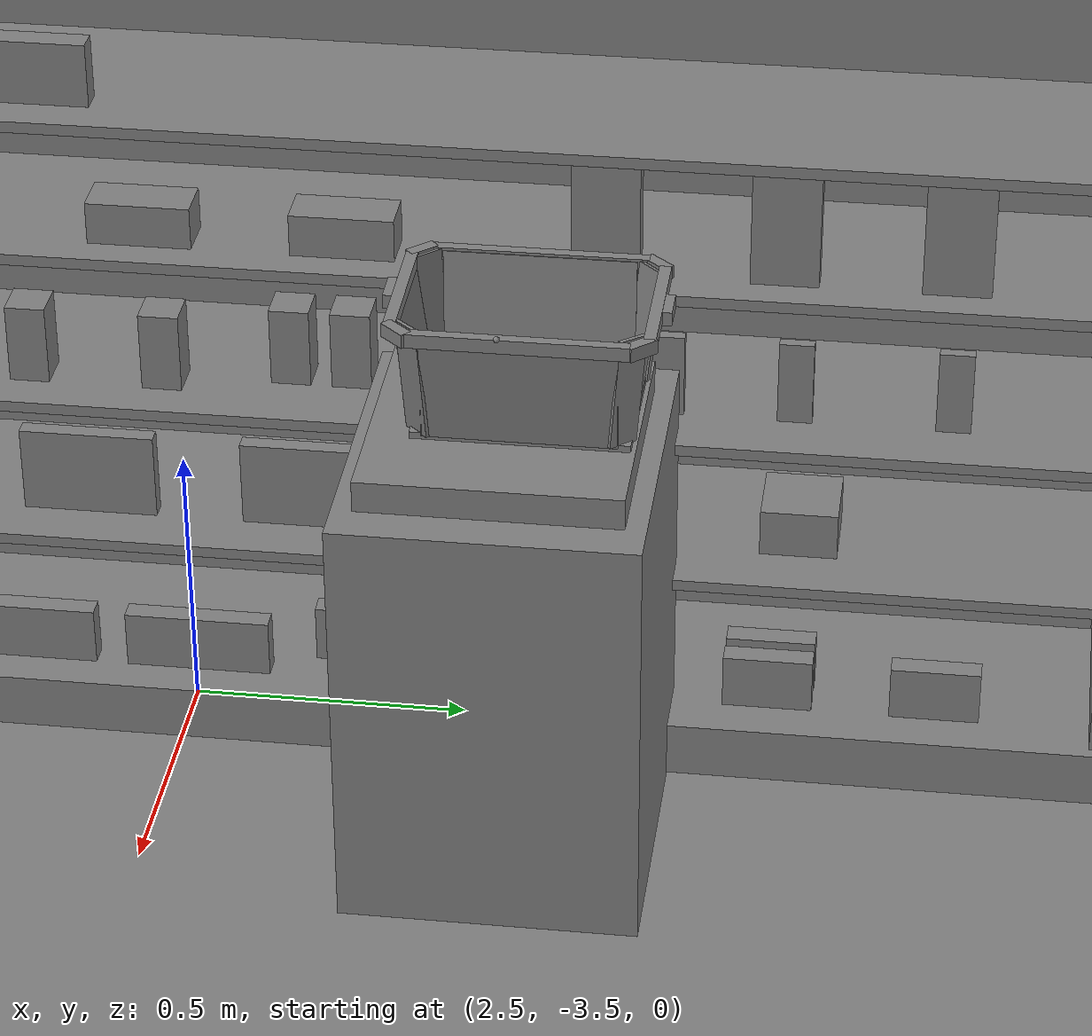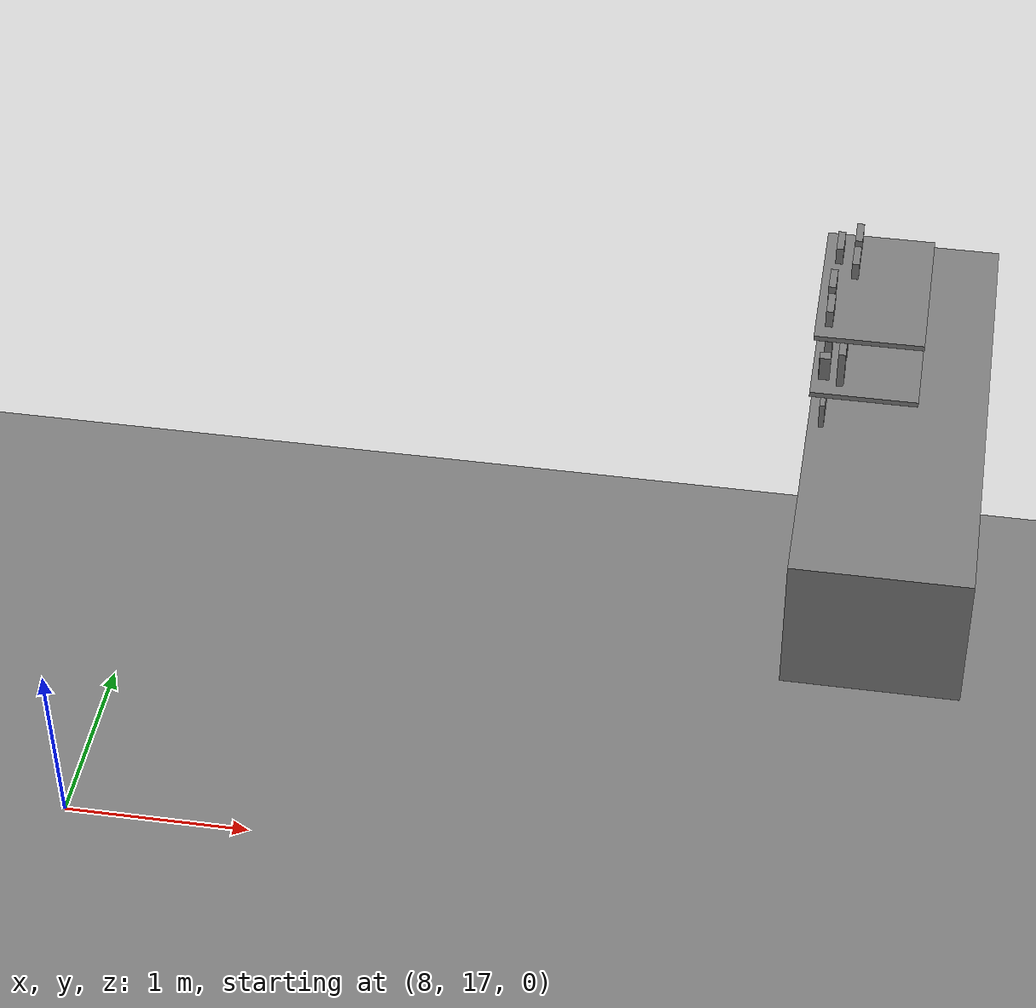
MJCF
<mujoco>
    <option gravity="0.000000000 0.000000000 -9.810000420" timestep="0.0166666" integrator="implicitfast" density="1.225" viscosity="1.8000001e-05" noslip_iterations="10" iterations="100" sdf_iterations="50">
        <flag multiccd="disable"/>
    </option>
    <size memory="1000M"/>
    <compiler coordinate="local"/>
    <worldbody>
        <light cutoff="30" pos="0 1 1" dir="0 -1 -2"/>
        <light cutoff="30" pos="0 -1 1" dir="0 1 -2"/>
        <body pos="2.497505903 -3.185120821 0.763295174" euler="0.000000000 0.000000000 0.000000000" name="openloong_gripper_2f85_fix_base_usda_jiazi_02_e_medicine_03_d">
            <geom contype="1" conaffinity="1" density="1000" type="box" material="" rgba="0.500000000 0.500000000 0.500000000 1.000000000" solimp="0.899999976 0.949999988 0.001000000" friction="1.000000000 0.005000000 0.000100000" solref="0.020000000 1.000000000" margin="0" condim="3" group="0" pos="0.000000000 0.000000000 0.000000000" quat="1.000000000 0.000000000 0.000000000 0.000000000" size="0.035000000 0.035000000 0.071999997" name="openloong_gripper_2f85_fix_base_usda_jiazi_02_e_medicine_03_d_F6BB0ADC_BF3D_4380_8C03_DE74FE9BEC44"/>
            <freejoint name="openloong_gripper_2f85_fix_base_usda_jiazi_02_e_medicine_03_d"/>
        </body>
        <body pos="2.859023094 -2.828485012 0.874997377" euler="89.999946594 0.000000000 0.000000000" name="openloong_gripper_2f85_fix_base_usda_MedicineChest">
            <geom contype="1" conaffinity="1" density="100000" type="box" material="" rgba="0.500000000 0.500000000 0.500000000 1.000000000" solimp="0.899999976 0.949999988 0.001000000" friction="1.000000000 0.899999976 0.000100000" solref="0.020000000 1.000000000" margin="0" condim="3" group="0" pos="-0.132964611 0.198016286 0.194559574" quat="0.359685898 -0.000000596 -0.933073401 0.000003695" size="0.010000000 0.012000000 0.026000001" name="openloong_gripper_2f85_fix_base_usda_geom_47D40BEF_4F8F_4A00_A328_B11A01FE6ACA"/>
            <geom contype="1" conaffinity="1" density="100000" type="box" material="" rgba="0.500000000 0.500000000 0.500000000 1.000000000" solimp="0.899999976 0.949999988 0.001000000" friction="1.000000000 0.899999976 0.000100000" solref="0.020000000 1.000000000" margin="0" condim="3" group="0" pos="0.000526667 0.104760587 -0.187798262" quat="0.705659389 -0.045368463 0.705640316 -0.045367181" size="0.003000000 0.100000001 0.100000001" name="openloong_gripper_2f85_fix_base_usda_geom_7F9CAB00_FD3A_4925_82C4_A8D3927D10EE"/>
            <geom contype="1" conaffinity="1" density="100000" type="box" material="" rgba="0.500000000 0.500000000 0.500000000 1.000000000" solimp="0.899999976 0.949999988 0.001000000" friction="1.000000000 0.899999976 0.000100000" solref="0.020000000 1.000000000" margin="0" condim="3" group="0" pos="-0.000797749 0.196027160 -0.223680258" quat="0.707158327 -0.000001520 0.707055092 -0.000001520" size="0.010000000 0.012000000 0.029999999" name="openloong_gripper_2f85_fix_base_usda_geom_686814DB_2D89_4208_ADBE_836D2BD95310"/>
            <geom contype="1" conaffinity="1" density="100000" type="box" material="" rgba="0.500000000 0.500000000 0.500000000 1.000000000" solimp="0.899999976 0.949999988 0.001000000" friction="1.000000000 0.899999976 0.000100000" solref="0.020000000 1.000000000" margin="0" condim="3" group="0" pos="0.000000000 0.005823255 0.000000000" quat="1.000000000 0.000000000 0.000000000 0.000000000" size="0.122000001 0.006000000 0.180000007" name="openloong_gripper_2f85_fix_base_usda_geom_AEFF7135_DBC8_44B9_B2C0_921E8FDD2CA8"/>
            <geom contype="1" conaffinity="1" density="100000" type="box" material="" rgba="0.500000000 0.500000000 0.500000000 1.000000000" solimp="0.899999976 0.949999988 0.001000000" friction="1.000000000 0.899999976 0.000100000" solref="0.020000000 1.000000000" margin="0" condim="3" group="0" pos="0.000516415 0.102862239 0.189926386" quat="0.705658197 0.045368552 0.705641508 0.045367509" size="0.003000000 0.100000001 0.100000001" name="openloong_gripper_2f85_fix_base_usda_geom_100A4A7B_D562_4B41_BDC2_335021EBFFB6"/>
            <geom contype="1" conaffinity="1" density="100000" type="box" material="" rgba="0.500000000 0.500000000 0.500000000 1.000000000" solimp="0.899999976 0.949999988 0.001000000" friction="1.000000000 0.899999976 0.000100000" solref="0.020000000 1.000000000" margin="0" condim="3" group="0" pos="-0.113059282 0.107842624 0.177997828" quat="0.369108677 0.045244619 -0.928185225 -0.013556212" size="0.003000000 0.100000001 0.026000001" name="openloong_gripper_2f85_fix_base_usda_geom_E4580B80_6770_4289_981B_0AA57485B5E7"/>
            <geom contype="1" conaffinity="1" density="100000" type="box" material="" rgba="0.500000000 0.500000000 0.500000000 1.000000000" solimp="0.899999976 0.949999988 0.001000000" friction="1.000000000 0.899999976 0.000100000" solref="0.020000000 1.000000000" margin="0" condim="3" group="0" pos="-0.000797749 0.196027160 0.223680258" quat="0.707158327 -0.000001520 0.707055092 -0.000001520" size="0.010000000 0.012000000 0.029999999" name="openloong_gripper_2f85_fix_base_usda_geom_B20F81CE_FBD5_470D_889C_4F80A84CCC3C"/>
            <geom contype="1" conaffinity="1" density="100000" type="box" material="" rgba="0.500000000 0.500000000 0.500000000 1.000000000" solimp="0.899999976 0.949999988 0.001000000" friction="1.000000000 0.899999976 0.000100000" solref="0.020000000 1.000000000" margin="0" condim="3" group="0" pos="0.128487587 0.105749547 0.000000238" quat="0.999090791 0.000000030 -0.000000002 -0.042632505" size="0.003000000 0.100000001 0.159999996" name="openloong_gripper_2f85_fix_base_usda_geom_5DF17C42_650F_448F_A0B8_07DF68C988CA"/>
            <geom contype="1" conaffinity="1" density="100000" type="box" material="" rgba="0.500000000 0.500000000 0.500000000 1.000000000" solimp="0.899999976 0.949999988 0.001000000" friction="1.000000000 0.899999976 0.000100000" solref="0.020000000 1.000000000" margin="0" condim="3" group="0" pos="-0.116801500 0.106451452 -0.175024986" quat="-0.356188178 0.039200634 -0.932773709 0.039071620" size="0.003000000 0.100000001 0.026000001" name="openloong_gripper_2f85_fix_base_usda_geom_0D7E1284_8F84_4580_8FB0_01DEAC1D256E"/>
            <geom contype="1" conaffinity="1" density="100000" type="box" material="" rgba="0.500000000 0.500000000 0.500000000 1.000000000" solimp="0.899999976 0.949999988 0.001000000" friction="1.000000000 0.899999976 0.000100000" solref="0.020000000 1.000000000" margin="0" condim="3" group="0" pos="0.000000715 0.198014379 0.208025932" quat="0.707159519 -0.000000089 0.707053959 -0.000000060" size="0.010000000 0.012000000 0.119999997" name="openloong_gripper_2f85_fix_base_usda_geom_E04A0C41_0A53_47C4_A89A_01FDD72B351A"/>
            <geom contype="1" conaffinity="1" density="100000" type="box" material="" rgba="0.500000000 0.500000000 0.500000000 1.000000000" solimp="0.899999976 0.949999988 0.001000000" friction="1.000000000 0.899999976 0.000100000" solref="0.020000000 1.000000000" margin="0" condim="3" group="0" pos="-0.133216143 0.198014021 -0.194619179" quat="-0.359760642 0.000001267 -0.933044553 0.000001341" size="0.010000000 0.012000000 0.026000001" name="openloong_gripper_2f85_fix_base_usda_geom_0C1E3FDD_9920_44D3_A0A0_49140A47EA1A"/>
            <geom contype="1" conaffinity="1" density="100000" type="box" material="" rgba="0.500000000 0.500000000 0.500000000 1.000000000" solimp="0.899999976 0.949999988 0.001000000" friction="1.000000000 0.899999976 0.000100000" solref="0.020000000 1.000000000" margin="0" condim="3" group="0" pos="0.115026236 0.107592762 0.174144983" quat="0.930772185 0.025311798 -0.363503337 -0.029796928" size="0.003000000 0.100000001 0.026000001" name="openloong_gripper_2f85_fix_base_usda_geom_E10EFD8C_F5F7_4FD7_986B_E2FBB732443B"/>
            <geom contype="1" conaffinity="1" density="100000" type="box" material="" rgba="0.500000000 0.500000000 0.500000000 1.000000000" solimp="0.899999976 0.949999988 0.001000000" friction="1.000000000 0.899999976 0.000100000" solref="0.020000000 1.000000000" margin="0" condim="3" group="0" pos="0.131582499 0.198014021 -0.194822311" quat="0.359707981 -0.000000596 -0.933064938 0.000003695" size="0.010000000 0.012000000 0.026000001" name="openloong_gripper_2f85_fix_base_usda_geom_F2882B74_5A06_41B0_9ACB_ACE854845097"/>
            <geom contype="1" conaffinity="1" density="100000" type="box" material="" rgba="0.500000000 0.500000000 0.500000000 1.000000000" solimp="0.899999976 0.949999988 0.001000000" friction="1.000000000 0.899999976 0.000100000" solref="0.020000000 1.000000000" margin="0" condim="3" group="0" pos="0.115736485 0.109648407 -0.172922373" quat="-0.356657803 0.026131347 0.933247149 -0.034088194" size="0.003000000 0.100000001 0.026000001" name="openloong_gripper_2f85_fix_base_usda_geom_68370751_B999_4429_9FAF_40A2B3D66667"/>
            <geom contype="1" conaffinity="1" density="100000" type="box" material="" rgba="0.500000000 0.500000000 0.500000000 1.000000000" solimp="0.899999976 0.949999988 0.001000000" friction="1.000000000 0.899999976 0.000100000" solref="0.020000000 1.000000000" margin="0" condim="3" group="0" pos="0.145289421 0.198014736 -0.000000238" quat="1.000000000 0.000000000 0.000000000 0.000000000" size="0.009000000 0.012000000 0.180000007" name="openloong_gripper_2f85_fix_base_usda_geom_35184CE7_A033_4BA3_8910_6EB8F2C17369"/>
            <geom contype="1" conaffinity="1" density="100000" type="box" material="" rgba="0.500000000 0.500000000 0.500000000 1.000000000" solimp="0.899999976 0.949999988 0.001000000" friction="1.000000000 0.899999976 0.000100000" solref="0.020000000 1.000000000" margin="0" condim="3" group="0" pos="0.000000715 0.198014379 -0.208025932" quat="0.707159519 -0.000000089 0.707053959 -0.000000060" size="0.010000000 0.012000000 0.119999997" name="openloong_gripper_2f85_fix_base_usda_geom_BF97195C_C8D0_4B81_98F8_733551CB0FE3"/>
            <geom contype="1" conaffinity="1" density="100000" type="box" material="" rgba="0.500000000 0.500000000 0.500000000 1.000000000" solimp="0.899999976 0.949999988 0.001000000" friction="1.000000000 0.899999976 0.000100000" solref="0.020000000 1.000000000" margin="0" condim="3" group="0" pos="-0.128487349 0.105749547 0.000000238" quat="0.999090791 0.000000030 -0.000000002 0.042632505" size="0.003000000 0.100000001 0.159999996" name="openloong_gripper_2f85_fix_base_usda_geom_909608FA_B595_4B08_AAA5_35319BD866B6"/>
            <geom contype="1" conaffinity="1" density="100000" type="box" material="" rgba="0.500000000 0.500000000 0.500000000 1.000000000" solimp="0.899999976 0.949999988 0.001000000" friction="1.000000000 0.899999976 0.000100000" solref="0.020000000 1.000000000" margin="0" condim="3" group="0" pos="-0.145288944 0.198014736 -0.000000238" quat="1.000000000 0.000000000 0.000000000 0.000000000" size="0.009000000 0.012000000 0.180000007" name="openloong_gripper_2f85_fix_base_usda_geom_9F086D6D_4F4E_43F0_96F5_8045EA9BAB02"/>
            <geom contype="1" conaffinity="1" density="100000" type="box" material="" rgba="0.500000000 0.500000000 0.500000000 1.000000000" solimp="0.899999976 0.949999988 0.001000000" friction="1.000000000 0.899999976 0.000100000" solref="0.020000000 1.000000000" margin="0" condim="3" group="0" pos="0.132833242 0.198015213 0.194798470" quat="-0.359736264 0.000001252 -0.933053970 0.000001401" size="0.010000000 0.012000000 0.026000001" name="openloong_gripper_2f85_fix_base_usda_geom_E98A50F7_4458_4A7D_94F1_50B0018F65BF"/>
            <freejoint name="openloong_gripper_2f85_fix_base_usda_MedicineChest_joint"/>
            <site size="0.005000000 0.005000000 0.005000000" rgba="0.500000000 0.500000000 0.500000000 1.000000000" pos="0.000000000 0.000000000 0.000000000" quat="1.000000000 0.000000000 0.000000000 0.000000000" group="0" type="sphere" name="openloong_gripper_2f85_fix_base_usda_MedicineChestsite"/>
        </body>
        <body pos="11.742162704 19.970987320 1.373408437" euler="0.000000000 0.000000000 -85.008651733" name="openloong_gripper_2f85_fix_base_usda_jiazi_02_e_medicine_11_pz_b">
            <geom contype="1" conaffinity="1" density="1000" type="box" material="" rgba="0.500000000 0.500000000 0.500000000 1.000000000" solimp="0.899999976 0.949999988 0.001000000" friction="1.000000000 0.005000000 0.000100000" solref="0.020000000 1.000000000" margin="0" condim="3" group="0" pos="0.000000000 0.000000000 0.000000000" quat="1.000000000 0.000000000 0.000000000 0.000000000" size="0.028000001 0.029999999 0.077000000" name="openloong_gripper_2f85_fix_base_usda_jiazi_02_e_medicine_11_pz_b_A1EECF91_BB9B_42DA_A27D_FD79C523F5AB"/>
            <freejoint name="openloong_gripper_2f85_fix_base_usda_jiazi_02_e_medicine_11_pz_b"/>
        </body>
        <body pos="2.540798664 -3.660816193 0.494465470" euler="0.000000000 0.000000000 0.000000000" name="openloong_gripper_2f85_fix_base_usda_jiazi_02_e_medicine_10_b">
            <geom contype="1" conaffinity="1" density="1000" type="box" material="" rgba="0.500000000 0.500000000 0.500000000 1.000000000" solimp="0.899999976 0.949999988 0.001000000" friction="1.000000000 0.005000000 0.000100000" solref="0.020000000 1.000000000" margin="0" condim="3" group="0" pos="0.000000000 0.000000000 0.000000000" quat="1.000000000 0.000000000 0.000000000 0.000000000" size="0.015000000 0.119999997 0.079000004" name="openloong_gripper_2f85_fix_base_usda_jiazi_02_e_medicine_10_b_3EA0FD14_6584_4A2B_8D39_ED8F77AB8964"/>
            <freejoint name="openloong_gripper_2f85_fix_base_usda_jiazi_02_e_medicine_10_b"/>
        </body>
        <body pos="2.540974617 -2.142210245 0.767729700" euler="0.000000000 0.000000000 0.000000000" name="openloong_gripper_2f85_fix_base_usda_jiazi_02_e_medicine_08_d">
            <geom contype="1" conaffinity="1" density="1000" type="box" material="" rgba="0.500000000 0.500000000 0.500000000 1.000000000" solimp="0.899999976 0.949999988 0.001000000" friction="1.000000000 0.005000000 0.000100000" solref="0.020000000 1.000000000" margin="0" condim="3" group="0" pos="0.000000000 0.000000000 0.000000000" quat="1.000000000 0.000000000 0.000000000 0.000000000" size="0.010000000 0.029999999 0.075999998" name="openloong_gripper_2f85_fix_base_usda_jiazi_02_e_medicine_08_d_DEDF22FC_1DC2_47FD_9DD4_EFE0ED4A20A0"/>
            <freejoint name="openloong_gripper_2f85_fix_base_usda_jiazi_02_e_medicine_08_d"/>
        </body>
        <body pos="2.617633820 -3.462228775 0.195964247" euler="0.000000000 0.000000000 0.000000000" name="openloong_gripper_2f85_fix_base_usda_jiazi_02_e_medicine_17_a">
            <geom contype="1" conaffinity="1" density="1000" type="box" material="" rgba="0.500000000 0.500000000 0.500000000 1.000000000" solimp="0.899999976 0.949999988 0.001000000" friction="1.000000000 0.005000000 0.000100000" solref="0.020000000 1.000000000" margin="0" condim="3" group="0" pos="0.000000000 0.000000000 0.000000000" quat="1.000000000 0.000000000 0.000000000 0.000000000" size="0.018999999 0.129999995 0.056000002" name="openloong_gripper_2f85_fix_base_usda_jiazi_02_e_medicine_17_a_4A2EACD9_D03F_4BDD_9C74_153BA7C93C7D"/>
            <freejoint name="openloong_gripper_2f85_fix_base_usda_jiazi_02_e_medicine_17_a"/>
        </body>
        <body pos="11.835501671 19.865364075 1.405766487" euler="0.000000000 0.000000000 0.000000000" name="openloong_gripper_2f85_fix_base_usda_jiazi_02_e_medicine_11_f">
            <geom contype="1" conaffinity="1" density="1000" type="box" material="" rgba="0.500000000 0.500000000 0.500000000 1.000000000" solimp="0.899999976 0.949999988 0.001000000" friction="1.000000000 0.005000000 0.000100000" solref="0.020000000 1.000000000" margin="0" condim="3" group="0" pos="0.000000000 0.000000000 0.000000000" quat="1.000000000 0.000000000 0.000000000 0.000000000" size="0.020000000 0.057999998 0.112999998" name="openloong_gripper_2f85_fix_base_usda_jiazi_02_e_medicine_11_f_286EEA0C_CABC_410E_9A62_EF8FE3E2C5EC"/>
            <freejoint name="openloong_gripper_2f85_fix_base_usda_jiazi_02_e_medicine_11_f"/>
        </body>
        <body pos="2.617633820 -3.779438972 0.195964247" euler="0.000000000 0.000000000 0.000000000" name="openloong_gripper_2f85_fix_base_usda_jiazi_02_e_medicine_17_b">
            <geom contype="1" conaffinity="1" density="1000" type="box" material="" rgba="0.500000000 0.500000000 0.500000000 1.000000000" solimp="0.899999976 0.949999988 0.001000000" friction="1.000000000 0.005000000 0.000100000" solref="0.020000000 1.000000000" margin="0" condim="3" group="0" pos="0.000000000 0.000000000 0.000000000" quat="1.000000000 0.000000000 0.000000000 0.000000000" size="0.018999999 0.129999995 0.056000002" name="openloong_gripper_2f85_fix_base_usda_jiazi_02_e_medicine_17_b_FF7408E0_82F0_47E3_90EB_4E617AB21CF7"/>
            <freejoint name="openloong_gripper_2f85_fix_base_usda_jiazi_02_e_medicine_17_b"/>
        </body>
        <body pos="11.758296013 20.215833664 1.746467471" euler="180.000000000 0.000000000 0.000000000" name="openloong_gripper_2f85_fix_base_usda_jiazi_02_e_medicine_16_e">
            <geom contype="1" conaffinity="1" density="1000" type="box" material="" rgba="0.500000000 0.500000000 0.500000000 1.000000000" solimp="0.899999976 0.949999988 0.001000000" friction="1.000000000 0.005000000 0.000100000" solref="0.020000000 1.000000000" margin="0" condim="3" group="0" pos="0.000000000 0.000000000 0.000000000" quat="0.000000000 1.000000000 0.000000000 0.000000000" size="0.020000000 0.079000004 0.052999999" name="openloong_gripper_2f85_fix_base_usda_jiazi_02_e_medicine_16_e_C7D7FA3E_E6C9_4134_BA65_50C4E24C21BC"/>
            <freejoint name="openloong_gripper_2f85_fix_base_usda_jiazi_02_e_medicine_16_e"/>
        </body>
        <body pos="2.527985811 -2.715100288 0.458167851" euler="0.000000000 0.000000000 0.000000000" name="openloong_gripper_2f85_fix_base_usda_jiazi_02_e_medicine_13_a">
            <geom contype="1" conaffinity="1" density="1000" type="box" material="" rgba="0.500000000 0.500000000 0.500000000 1.000000000" solimp="0.899999976 0.949999988 0.001000000" friction="1.000000000 0.005000000 0.000100000" solref="0.020000000 1.000000000" margin="0" condim="3" group="0" pos="0.000000000 0.000000000 0.000000000" quat="1.000000000 0.000000000 0.000000000 0.000000000" size="0.067000002 0.068000004 0.044000000" name="openloong_gripper_2f85_fix_base_usda_jiazi_02_e_medicine_13_a_4B7A4995_0B78_4C95_9496_B04B368BA555"/>
            <freejoint name="openloong_gripper_2f85_fix_base_usda_jiazi_02_e_medicine_13_a"/>
        </body>
        <body pos="2.557055712 -3.127499342 0.195964247" euler="0.000000000 0.000000000 0.000000000" name="openloong_gripper_2f85_fix_base_usda_jiazi_02_e_medicine_17_c">
            <geom contype="1" conaffinity="1" density="1000" type="box" material="" rgba="0.500000000 0.500000000 0.500000000 1.000000000" solimp="0.899999976 0.949999988 0.001000000" friction="1.000000000 0.005000000 0.000100000" solref="0.020000000 1.000000000" margin="0" condim="3" group="0" pos="0.000000000 0.000000000 0.000000000" quat="1.000000000 0.000000000 0.000000000 0.000000000" size="0.018999999 0.129999995 0.056000002" name="openloong_gripper_2f85_fix_base_usda_jiazi_02_e_medicine_17_c_81D9FF82_5328_40B1_8671_91C8C9BB06EE"/>
            <freejoint name="openloong_gripper_2f85_fix_base_usda_jiazi_02_e_medicine_17_c"/>
        </body>
        <body pos="2.555686235 -2.149417400 1.079351544" euler="0.000000000 0.000000000 0.000000000" name="openloong_gripper_2f85_fix_base_usda_jiazi_02_e_medicine_11_b">
            <geom contype="1" conaffinity="1" density="1000" type="box" material="" rgba="0.500000000 0.500000000 0.500000000 1.000000000" solimp="0.899999976 0.949999988 0.001000000" friction="1.000000000 0.005000000 0.000100000" solref="0.020000000 1.000000000" margin="0" condim="3" group="0" pos="0.000000000 0.000000000 0.000000000" quat="1.000000000 0.000000000 0.000000000 0.000000000" size="0.020000000 0.057999998 0.112999998" name="openloong_gripper_2f85_fix_base_usda_jiazi_02_e_medicine_11_b_55987314_5311_4695_B785_710D9EF33E5E"/>
            <freejoint name="openloong_gripper_2f85_fix_base_usda_jiazi_02_e_medicine_11_b"/>
        </body>
        <body pos="2.540974617 -2.413386345 0.767729700" euler="0.000000000 0.000000000 0.000000000" name="openloong_gripper_2f85_fix_base_usda_jiazi_02_e_medicine_08_c">
            <geom contype="1" conaffinity="1" density="1000" type="box" material="" rgba="0.500000000 0.500000000 0.500000000 1.000000000" solimp="0.899999976 0.949999988 0.001000000" friction="1.000000000 0.005000000 0.000100000" solref="0.020000000 1.000000000" margin="0" condim="3" group="0" pos="0.000000000 0.000000000 0.000000000" quat="1.000000000 0.000000000 0.000000000 0.000000000" size="0.010000000 0.029999999 0.075999998" name="openloong_gripper_2f85_fix_base_usda_jiazi_02_e_medicine_08_c_ADCAA66C_A0F3_42FF_B929_3DC606FC0CDB"/>
            <freejoint name="openloong_gripper_2f85_fix_base_usda_jiazi_02_e_medicine_08_c"/>
        </body>
        <body pos="2.546508551 -2.439894676 0.193254441" euler="0.000000000 0.000000000 0.000000000" name="openloong_gripper_2f85_fix_base_usda_jiazi_02_e_medicine_16_a">
            <geom contype="1" conaffinity="1" density="1000" type="box" material="" rgba="0.500000000 0.500000000 0.500000000 1.000000000" solimp="0.899999976 0.949999988 0.001000000" friction="1.000000000 0.005000000 0.000100000" solref="0.020000000 1.000000000" margin="0" condim="3" group="0" pos="0.000000000 0.000000000 0.000000000" quat="1.000000000 0.000000000 0.000000000 0.000000000" size="0.020000000 0.079000004 0.052999999" name="openloong_gripper_2f85_fix_base_usda_jiazi_02_e_medicine_16_a_52BF894B_B5A4_4460_BAE8_489B80AD8E62"/>
            <freejoint name="openloong_gripper_2f85_fix_base_usda_jiazi_02_e_medicine_16_a"/>
        </body>
        <body pos="2.540974617 -2.634179592 0.767729700" euler="0.000000000 0.000000000 0.000000000" name="openloong_gripper_2f85_fix_base_usda_jiazi_02_e_medicine_08_b">
            <geom contype="1" conaffinity="1" density="1000" type="box" material="" rgba="0.500000000 0.500000000 0.500000000 1.000000000" solimp="0.899999976 0.949999988 0.001000000" friction="1.000000000 0.005000000 0.000100000" solref="0.020000000 1.000000000" margin="0" condim="3" group="0" pos="0.000000000 0.000000000 0.000000000" quat="1.000000000 0.000000000 0.000000000 0.000000000" size="0.010000000 0.029999999 0.075999998" name="openloong_gripper_2f85_fix_base_usda_jiazi_02_e_medicine_08_b_A1DB0737_A6CC_470B_B68A_E43B619A0C58"/>
            <freejoint name="openloong_gripper_2f85_fix_base_usda_jiazi_02_e_medicine_08_b"/>
        </body>
        <body pos="0.000000000 0.000000000 0.000000000" euler="0.000000000 0.000000000 0.000000000" name="Static Objcets_Static Objcets">
            <geom contype="1" conaffinity="1" density="1000" type="box" material="" rgba="0.500000000 0.500000000 0.500000000 1.000000000" solimp="0.899999976 0.959999979 0.001000000" friction="1.000000000 0.005000000 0.000100000" solref="0.020000000 1.000000000" margin="0" condim="3" group="0" pos="2.433294058 -2.920555353 0.961130261" quat="1.000000000 0.000000000 0.000000000 0.000000000" size="0.200000003 1.100000024 0.010000000" name="Static Objcets_SM_jiazi_02_e_D46FC458_F859_4384_BADB_296D9E403C8C"/>
            <geom contype="1" conaffinity="1" density="1000" type="box" material="" rgba="0.500000000 0.500000000 0.500000000 1.000000000" solimp="0.899999976 0.949999988 0.001000000" friction="1.000000000 0.005000000 0.000100000" solref="0.020000000 1.000000000" margin="0" condim="3" group="0" pos="2.064697266 -2.945113420 0.768164337" quat="1.000000000 0.000000000 0.000000000 0.000000000" size="0.200000003 1.100000024 0.750000000" name="Static Objcets_SM_jiazi_02_c_39F10989_D082_4A86_9EE6_8BEB4AF18ED5"/>
            <geom contype="1" conaffinity="1" density="1000" type="box" material="" rgba="0.500000000 0.500000000 0.500000000 1.000000000" solimp="0.899999976 0.949999988 0.001000000" friction="1.000000000 0.005000000 0.000100000" solref="0.020000000 1.000000000" margin="0" condim="3" group="0" pos="2.285422325 -1.621193886 0.671916366" quat="1.000000000 0.000000000 0.000000000 0.000000000" size="0.400000006 0.250000000 0.649999976" name="Static Objcets_SM_jiazi_02_a_479D315C_2FB8_4F0C_AE3B_069BD5EB8C86"/>
            <geom contype="1" conaffinity="1" density="1000" type="box" material="" rgba="0.500000000 0.500000000 0.500000000 1.000000000" solimp="0.899999976 0.959999979 0.001000000" friction="1.000000000 0.005000000 0.000100000" solref="0.020000000 1.000000000" margin="0" condim="3" group="0" pos="2.506457806 -2.919259548 0.097404450" quat="1.000000000 0.000000000 0.000000000 0.000000000" size="0.200000003 1.100000024 0.050000001" name="Static Objcets_SM_jiazi_02_h_FD6B8888_9DA4_4A33_B79E_993A36B081D4"/>
            <geom contype="1" conaffinity="1" density="1000" type="box" material="" rgba="0.500000000 0.500000000 0.500000000 1.000000000" solimp="0.899999976 0.949999988 0.001000000" friction="1.000000000 0.005000000 0.000100000" solref="0.020000000 1.000000000" margin="0" condim="3" group="0" pos="2.285422325 -4.217127323 0.670601368" quat="1.000000000 0.000000000 0.000000000 0.000000000" size="0.400000006 0.250000000 0.649999976" name="Static Objcets_SM_jiazi_02_b_74BC2974_2281_4E93_A984_6DCE3A0EA221"/>
            <geom contype="1" conaffinity="1" density="1000" type="box" material="" rgba="0.500000000 0.500000000 0.500000000 1.000000000" solimp="0.899999976 0.959999979 0.001000000" friction="1.000000000 0.005000000 0.000100000" solref="0.020000000 1.000000000" margin="0" condim="3" group="0" pos="2.452836037 -2.920555353 0.682593882" quat="1.000000000 0.000000000 0.000000000 0.000000000" size="0.200000003 1.100000024 0.010000000" name="Static Objcets_SM_jiazi_02_f_8BAA146D_6416_496A_91ED_12A6A72BF205"/>
            <geom contype="1" conaffinity="1" density="1000" type="box" material="" rgba="0.500000000 0.500000000 0.500000000 1.000000000" solimp="0.899999976 0.959999979 0.001000000" friction="1.000000000 0.005000000 0.000100000" solref="0.020000000 1.000000000" margin="0" condim="3" group="0" pos="2.437276840 -2.920555353 1.214537978" quat="1.000000000 0.000000000 0.000000000 0.000000000" size="0.200000003 1.100000024 0.010000000" name="Static Objcets_SM_jiazi_02_d_49E4D35B_E2D4_4E86_B864_45A88A507449"/>
            <geom contype="1" conaffinity="1" density="1000" type="box" material="" rgba="0.500000000 0.500000000 0.500000000 1.000000000" solimp="0.899999976 0.959999979 0.001000000" friction="1.000000000 0.005000000 0.000100000" solref="0.020000000 1.000000000" margin="0" condim="3" group="0" pos="2.448674917 -2.920555353 0.406362146" quat="1.000000000 0.000000000 0.000000000 0.000000000" size="0.200000003 1.100000024 0.010000000" name="Static Objcets_SM_jiazi_02_g_CCBFEDCD_31D2_4693_8F4A_E3798F954D70"/>
            <geom contype="1" conaffinity="1" density="1000" type="box" material="" rgba="0.500000000 0.500000000 0.500000000 1.000000000" solimp="0.899999976 0.959999979 0.001000000" friction="1.000000000 0.005000000 0.000100000" solref="0.020000000 1.000000000" margin="0" condim="3" group="0" pos="11.976007462 19.950820923 1.679351807" quat="1.000000000 0.000000000 0.000000000 0.000000000" size="0.300000012 0.460000008 0.015000000" name="Static Objcets_SM_guizi_06_c_09434E42_3716_4EBA_82F0_A92447345186"/>
            <geom contype="1" conaffinity="1" density="1000" type="box" material="" rgba="0.500000000 0.500000000 0.500000000 1.000000000" solimp="0.899999976 0.959999979 0.001000000" friction="1.000000000 0.005000000 0.000100000" solref="0.020000000 1.000000000" margin="0" condim="3" group="0" pos="12.172613144 19.933198929 0.307627976" quat="1.000000000 0.000000000 0.000000000 0.000000000" size="0.500000000 1.450000048 0.600000024" name="Static Objcets_SM_guizi_06_a_3E876ADC_1451_4540_967C_727D1B9DCCAB"/>
            <geom contype="1" conaffinity="1" density="1000" type="plane" material="" rgba="0.500000000 0.500000000 0.500000000 1.000000000" solimp="0.899999976 0.949999988 0.001000000" friction="1.000000000 0.005000000 0.000100000" solref="0.020000000 1.000000000" margin="0" condim="3" group="0" pos="0.000000000 0.000000000 0.042896956" quat="1.000000000 0.000000000 0.000000000 0.000000000" size="20.000000000 20.000000000 1.000000000" name="Static Objcets_floor_DA829C10_A2AA_4A0D_9E65_3905A7AF48C8"/>
            <geom contype="1" conaffinity="1" density="1000" type="box" material="" rgba="0.500000000 0.500000000 0.500000000 1.000000000" solimp="0.899999976 0.959999979 0.001000000" friction="1.000000000 0.005000000 0.000100000" solref="0.020000000 1.000000000" margin="0" condim="3" group="0" pos="11.976007462 19.948400497 1.278063059" quat="1.000000000 0.000000000 0.000000000 0.000000000" size="0.300000012 0.460000008 0.015000000" name="Static Objcets_SM_guizi_06_b_A82011C5_80C7_44B3_94B9_D3560A1B84EE"/>
        </body>
        <body pos="0.000000000 0.000000000 0.000000000" euler="0.000000000 0.000000000 0.000000000" name="Interactive Objcets_Interactive Objcets"/>
        <body pos="2.981746674 -2.307318449 1.336120248" euler="2.421562433 -33.497707367 38.191455841" mocap="true" name="spotlight1_SpotLight"/>
        <body pos="1000.000000000 1000.000000000 1.000000000" euler="0.000000000 0.000000000 0.000000000" name="openloong_gripper_2f85_fix_base_usda_niuhuangwan">
            <geom contype="1" conaffinity="1" density="1000" type="box" material="" rgba="0.500000000 0.500000000 0.500000000 1.000000000" solimp="0.899999976 0.949999988 0.001000000" friction="1.000000000 0.005000000 0.000100000" solref="0.020000000 1.000000000" margin="0" condim="3" group="0" mass="0.5" pos="0.000000000 0.000000000 0.040254507" quat="1.000000000 0.000000000 0.000000000 0.000000000" size="0.014699999 0.096599996 0.041999999" name="openloong_gripper_2f85_fix_base_usda_niuhuangwan_A9A480B5_FD61_4871_B728_EECADF1E9678"/>
            <freejoint name="openloong_gripper_2f85_fix_base_usda_niuhuangwan_joint"/>
            <site size="0.005000000 0.005000000 0.005000000" rgba="0.500000000 0.500000000 0.500000000 1.000000000" pos="0.000000000 0.000000000 0.000000000" quat="0.999961913 0.008726500 0.000000000 0.000000000" group="0" type="sphere" name="openloong_gripper_2f85_fix_base_usda_niuhuangwansite"/>
        </body>
        <body pos="2.819007874 -3.037729263 1.302561998" euler="166.154785156 41.517131805 59.168449402" mocap="true" name="spotlight3_SpotLight"/>
        <body pos="1000.000000000 1000.000000000 1.000000000" euler="0.000000000 0.000000000 0.000000000" name="openloong_gripper_2f85_fix_base_usda_qinghuopian">
            <geom contype="1" conaffinity="1" density="1000" type="box" material="" rgba="0.500000000 0.500000000 0.500000000 1.000000000" solimp="0.899999976 0.949999988 0.001000000" friction="1.000000000 0.005000000 0.000100000" solref="0.020000000 1.000000000" margin="0" condim="3" group="0" mass="0.5" pos="0.000000000 0.000000000 0.036895368" quat="1.000000000 0.000000000 0.000000000 0.000000000" size="0.014000000 0.055300001 0.037099998" name="openloong_gripper_2f85_fix_base_usda_jiazi_02_e_medicine_16_b_21D8CE24_4DD3_40D9_A024_982E575CD833"/>
            <freejoint name="openloong_gripper_2f85_fix_base_usda_qinghuopian_joint"/>
            <site size="0.005000000 0.005000000 0.005000000" rgba="0.500000000 0.500000000 0.500000000 1.000000000" pos="0.000000000 0.000000000 0.000000000" quat="0.999961913 0.008726534 0.000000000 0.000000000" group="0" type="sphere" name="openloong_gripper_2f85_fix_base_usda_qinghuopiansite"/>
        </body>
        <body pos="3.030014753 -2.624136686 1.396029353" euler="-88.295372009 -37.257534027 113.377502441" mocap="true" name="spotlight5_SpotLight"/>
        <body pos="1000.000000000 1000.000000000 1.000000000" euler="0.000000000 0.000000000 0.000000000" name="openloong_gripper_2f85_fix_base_usda_xiaokepian">
            <geom contype="1" conaffinity="1" density="1000" type="box" material="" rgba="0.500000000 0.500000000 0.500000000 1.000000000" solimp="0.899999976 0.949999988 0.001000000" friction="1.000000000 0.005000000 0.000100000" solref="0.020000000 1.000000000" margin="0" condim="3" group="0" mass="0.5" pos="0.000000000 0.000000000 0.055557761" quat="1.000000000 0.000000000 0.000000000 0.000000000" size="0.011900000 0.083999999 0.055999998" name="openloong_gripper_2f85_fix_base_usda_jiazi_02_e_medicine_10_a_04FE2369_9C1B_40A6_80EC_37ECA4B96463"/>
            <freejoint name="openloong_gripper_2f85_fix_base_usda_xiaokepian_joint"/>
            <site size="0.005000000 0.005000000 0.005000000" rgba="0.500000000 0.500000000 0.500000000 1.000000000" pos="0.000000000 0.000000000 0.000000000" quat="0.999961913 0.008726534 0.000000000 0.000000000" group="0" type="sphere" name="openloong_gripper_2f85_fix_base_usda_xiaokepiansite"/>
        </body>
        <body pos="1000.000000000 1000.000000000 1.000000000" euler="0.000000000 0.000000000 0.000000000" name="openloong_gripper_2f85_fix_base_usda_pipalu">
            <geom contype="1" conaffinity="1" density="1000" type="box" material="" rgba="0.500000000 0.500000000 0.500000000 1.000000000" solimp="0.899999976 0.949999988 0.001000000" friction="1.000000000 0.005000000 0.000100000" solref="0.020000000 1.000000000" margin="0" condim="3" group="0" mass="0.5" pos="0.000000000 0.000000000 0.053639743" quat="1.000000000 0.000000000 0.000000000 0.000000000" size="0.011900000 0.023100000 0.053900000" name="openloong_gripper_2f85_fix_base_usda_jiazi_02_e_medicine_08_a_F1B0EBD9_ED80_4088_9B63_01743DF03732"/>
            <freejoint name="openloong_gripper_2f85_fix_base_usda_pipalu_joint"/>
            <site size="0.005000000 0.005000000 0.005000000" rgba="0.500000000 0.500000000 0.500000000 1.000000000" pos="0.000000000 0.000000000 0.000000000" quat="0.999961913 0.008726534 0.000000000 0.000000000" group="0" type="sphere" name="openloong_gripper_2f85_fix_base_usda_pipalusite"/>
        </body>
        <body pos="1000.000000000 1000.000000000 1.000000000" euler="0.000000000 0.000000000 0.000000000" name="openloong_gripper_2f85_fix_base_usda_orangebox">
            <geom contype="1" conaffinity="1" density="1000" type="box" material="" rgba="0.500000000 0.500000000 0.500000000 1.000000000" solimp="0.899999976 0.949999988 0.001000000" friction="1.000000000 0.005000000 0.000100000" solref="0.020000000 1.000000000" margin="0" condim="3" group="0" mass="0.5" pos="0.000000000 0.000000000 0.051213536" quat="1.000000000 0.000000000 0.000000000 0.000000000" size="0.024499999 0.024499999 0.051099997" name="openloong_gripper_2f85_fix_base_usda_jiazi_02_e_medicine_03_a_766B0F0D_37EB_4DB8_AB6B_C81AA87546C6"/>
            <freejoint name="openloong_gripper_2f85_fix_base_usda_orangebox_joint"/>
            <site size="0.005000000 0.005000000 0.005000000" rgba="0.500000000 0.500000000 0.500000000 1.000000000" pos="0.000000000 0.000000000 0.000000000" quat="0.999961913 0.008726535 0.000000000 0.000000000" group="0" type="sphere" name="openloong_gripper_2f85_fix_base_usda_orangeboxsite"/>
        </body>
        <body pos="2.877940178 -2.751950979 0.062857389" euler="0.000000000 0.000000000 0.000000000" name="[25330501543951]_DeliveryRobot_01">
            <geom contype="1" conaffinity="1" density="1000" type="box" material="" rgba="0.500000000 0.500000000 0.500000000 1.000000000" solimp="0.899999976 0.949999988 0.001000000" friction="1.000000000 0.005000000 0.000100000" solref="0.020000000 1.000000000" margin="0" condim="3" group="0" pos="0.000000000 -0.111846209 0.319800019" quat="1.000000000 0.000000000 0.000000000 0.000000000" size="0.289999992 0.254999995 0.419999987" name="[25330501543951]_geom_6B70019A_6F47_4187_920D_6297098D0933"/>
            <geom contype="1" conaffinity="1" density="1000" type="box" material="" rgba="0.500000000 0.500000000 0.500000000 1.000000000" solimp="0.899999976 0.949999988 0.001000000" friction="1.000000000 0.005000000 0.000100000" solref="0.020000000 1.000000000" margin="0" condim="3" group="0" pos="0.000000000 -0.111846209 0.744405389" quat="1.000000000 0.000000000 0.000000000 0.000000000" size="0.219999999 0.219999999 0.050000001" name="[25330501543951]_geom_AAEE900F_C346_4863_BFD9_BA4E12CBDED7"/>
        </body>
        <body pos="2.497505903 -3.292093039 0.763295174" euler="0.000000000 0.000000000 0.000000000" name="openloong_gripper_2f85_fix_base_usda_jiazi_02_e_medicine_03_c">
            <geom contype="1" conaffinity="1" density="1000" type="box" material="" rgba="0.500000000 0.500000000 0.500000000 1.000000000" solimp="0.899999976 0.949999988 0.001000000" friction="1.000000000 0.005000000 0.000100000" solref="0.020000000 1.000000000" margin="0" condim="3" group="0" pos="0.000000000 0.000000000 0.000000000" quat="1.000000000 0.000000000 0.000000000 0.000000000" size="0.035000000 0.035000000 0.071999997" name="openloong_gripper_2f85_fix_base_usda_jiazi_02_e_medicine_03_c_5C80AC93_15FB_49C7_B04C_DCB6BCA1DC29"/>
            <freejoint name="openloong_gripper_2f85_fix_base_usda_jiazi_02_e_medicine_03_c"/>
        </body>
        <body pos="11.763878822 20.100526810 1.405766487" euler="0.000000000 0.000000000 0.000000000" name="openloong_gripper_2f85_fix_base_usda_jiazi_02_e_medicine_11_d">
            <geom contype="1" conaffinity="1" density="1000" type="box" material="" rgba="0.500000000 0.500000000 0.500000000 1.000000000" solimp="0.899999976 0.949999988 0.001000000" friction="1.000000000 0.005000000 0.000100000" solref="0.020000000 1.000000000" margin="0" condim="3" group="0" pos="0.000000000 0.000000000 0.000000000" quat="1.000000000 0.000000000 0.000000000 0.000000000" size="0.020000000 0.057999998 0.112999998" name="openloong_gripper_2f85_fix_base_usda_jiazi_02_e_medicine_11_d_418D169D_A780_46DF_9D43_7DCA8C950F63"/>
            <freejoint name="openloong_gripper_2f85_fix_base_usda_jiazi_02_e_medicine_11_d"/>
        </body>
        <body pos="11.742162704 19.632486343 1.369683743" euler="0.000000000 0.000000000 -85.008651733" name="openloong_gripper_2f85_fix_base_usda_jiazi_02_e_medicine_11_pz_a">
            <geom contype="1" conaffinity="1" density="1000" type="box" material="" rgba="0.500000000 0.500000000 0.500000000 1.000000000" solimp="0.899999976 0.949999988 0.001000000" friction="1.000000000 0.005000000 0.000100000" solref="0.020000000 1.000000000" margin="0" condim="3" group="0" pos="0.000000000 0.000000000 0.000000000" quat="1.000000000 0.000000000 0.000000000 0.000000000" size="0.028000001 0.029999999 0.077000000" name="openloong_gripper_2f85_fix_base_usda_jiazi_02_e_medicine_11_pz_a_58BEBF0A_C535_4A65_978F_A6E542B70A1F"/>
            <freejoint name="openloong_gripper_2f85_fix_base_usda_jiazi_02_e_medicine_11_pz_a"/>
        </body>
        <body pos="11.835501671 19.621755600 1.405766487" euler="0.000000000 0.000000000 0.000000000" name="openloong_gripper_2f85_fix_base_usda_jiazi_02_e_medicine_11_g">
            <geom contype="1" conaffinity="1" density="1000" type="box" material="" rgba="0.500000000 0.500000000 0.500000000 1.000000000" solimp="0.899999976 0.949999988 0.001000000" friction="1.000000000 0.005000000 0.000100000" solref="0.020000000 1.000000000" margin="0" condim="3" group="0" pos="0.000000000 0.000000000 0.000000000" quat="1.000000000 0.000000000 0.000000000 0.000000000" size="0.020000000 0.057999998 0.112999998" name="openloong_gripper_2f85_fix_base_usda_jiazi_02_e_medicine_11_g_F71102B3_954B_4A99_B281_2A39BCEA79C6"/>
            <freejoint name="openloong_gripper_2f85_fix_base_usda_jiazi_02_e_medicine_11_g"/>
        </body>
        <body pos="2.608781099 -2.439894676 0.193254441" euler="0.000000000 0.000000000 0.000000000" name="openloong_gripper_2f85_fix_base_usda_jiazi_02_e_medicine_16_b">
            <geom contype="1" conaffinity="1" density="1000" type="box" material="" rgba="0.500000000 0.500000000 0.500000000 1.000000000" solimp="0.899999976 0.949999988 0.001000000" friction="1.000000000 0.005000000 0.000100000" solref="0.020000000 1.000000000" margin="0" condim="3" group="0" pos="0.000000000 0.000000000 0.000000000" quat="1.000000000 0.000000000 0.000000000 0.000000000" size="0.020000000 0.079000004 0.052999999" name="openloong_gripper_2f85_fix_base_usda_jiazi_02_e_medicine_16_b_749068C5_E4BB_431C_A571_A5DAD7CDF19D"/>
            <freejoint name="openloong_gripper_2f85_fix_base_usda_jiazi_02_e_medicine_16_b"/>
        </body>
        <body pos="2.535823345 -3.535886526 1.006494284" euler="0.000000000 0.000000000 0.000000000" name="openloong_gripper_2f85_fix_base_usda_jiazi_02_e_medicine_01_a">
            <geom contype="1" conaffinity="1" density="1000" type="box" material="" rgba="0.500000000 0.500000000 0.500000000 1.000000000" solimp="0.899999976 0.949999988 0.001000000" friction="1.000000000 0.005000000 0.000100000" solref="0.020000000 1.000000000" margin="0" condim="3" group="0" pos="0.000000000 0.000000000 0.000000000" quat="1.000000000 0.000000000 0.000000000 0.000000000" size="0.039999999 0.090000004 0.039999999" name="openloong_gripper_2f85_fix_base_usda_jiazi_02_e_medicine_01_a_9F7DA274_3714_4D2E_9F38_EE8D41946D91"/>
            <freejoint name="openloong_gripper_2f85_fix_base_usda_jiazi_02_e_medicine_01_a"/>
        </body>
        <body pos="2.535823345 -3.186250448 1.006494284" euler="0.000000000 0.000000000 0.000000000" name="openloong_gripper_2f85_fix_base_usda_jiazi_02_e_medicine_01_b">
            <geom contype="1" conaffinity="1" density="1000" type="box" material="" rgba="0.500000000 0.500000000 0.500000000 1.000000000" solimp="0.899999976 0.949999988 0.001000000" friction="1.000000000 0.005000000 0.000100000" solref="0.020000000 1.000000000" margin="0" condim="3" group="0" pos="0.000000000 0.000000000 0.000000000" quat="1.000000000 0.000000000 0.000000000 0.000000000" size="0.039999999 0.090000004 0.039999999" name="openloong_gripper_2f85_fix_base_usda_jiazi_02_e_medicine_01_b_F5FFF3D9_52A5_42DE_8B17_608A75F0605E"/>
            <freejoint name="openloong_gripper_2f85_fix_base_usda_jiazi_02_e_medicine_01_b"/>
        </body>
        <body pos="2.619754076 -2.721762657 0.193254441" euler="0.000000000 0.000000000 0.000000000" name="openloong_gripper_2f85_fix_base_usda_jiazi_02_e_medicine_16_d">
            <geom contype="1" conaffinity="1" density="1000" type="box" material="" rgba="0.500000000 0.500000000 0.500000000 1.000000000" solimp="0.899999976 0.949999988 0.001000000" friction="1.000000000 0.005000000 0.000100000" solref="0.020000000 1.000000000" margin="0" condim="3" group="0" pos="0.000000000 0.000000000 0.000000000" quat="1.000000000 0.000000000 0.000000000 0.000000000" size="0.020000000 0.079000004 0.052999999" name="openloong_gripper_2f85_fix_base_usda_jiazi_02_e_medicine_16_d_0441CC1F_FEAC_4DED_ADC5_545C0F02DFD0"/>
            <freejoint name="openloong_gripper_2f85_fix_base_usda_jiazi_02_e_medicine_16_d"/>
        </body>
        <body pos="11.742162704 20.304208755 1.369683743" euler="0.000000000 0.000000000 -85.008651733" name="openloong_gripper_2f85_fix_base_usda_jiazi_02_e_medicine_11_pz_c">
            <geom contype="1" conaffinity="1" density="1000" type="box" material="" rgba="0.500000000 0.500000000 0.500000000 1.000000000" solimp="0.899999976 0.949999988 0.001000000" friction="1.000000000 0.005000000 0.000100000" solref="0.020000000 1.000000000" margin="0" condim="3" group="0" pos="0.000000000 0.000000000 0.000000000" quat="1.000000000 0.000000000 0.000000000 0.000000000" size="0.028000001 0.029999999 0.077000000" name="openloong_gripper_2f85_fix_base_usda_jiazi_02_e_medicine_11_pz_c_4AA12F38_8818_4FA0_8491_E81057E211BB"/>
            <freejoint name="openloong_gripper_2f85_fix_base_usda_jiazi_02_e_medicine_11_pz_c"/>
        </body>
        <body pos="11.749706268 19.659208298 1.746467471" euler="180.000000000 0.000000000 0.000000000" name="openloong_gripper_2f85_fix_base_usda_jiazi_02_e_medicine_16_g">
            <geom contype="1" conaffinity="1" density="1000" type="box" material="" rgba="0.500000000 0.500000000 0.500000000 1.000000000" solimp="0.899999976 0.949999988 0.001000000" friction="1.000000000 0.005000000 0.000100000" solref="0.020000000 1.000000000" margin="0" condim="3" group="0" pos="0.000000000 0.000000000 0.000000000" quat="0.000000000 1.000000000 0.000000000 0.000000000" size="0.020000000 0.079000004 0.052999999" name="openloong_gripper_2f85_fix_base_usda_jiazi_02_e_medicine_16_g_BFF88F04_EFA5_495D_960F_A2705F54D1C6"/>
            <freejoint name="openloong_gripper_2f85_fix_base_usda_jiazi_02_e_medicine_16_g"/>
        </body>
        <body pos="11.742162704 20.226203918 1.369683743" euler="0.000000000 0.000000000 -85.008651733" name="openloong_gripper_2f85_fix_base_usda_jiazi_02_e_medicine_11_pz_d">
            <geom contype="1" conaffinity="1" density="1000" type="box" material="" rgba="0.500000000 0.500000000 0.500000000 1.000000000" solimp="0.899999976 0.949999988 0.001000000" friction="1.000000000 0.005000000 0.000100000" solref="0.020000000 1.000000000" margin="0" condim="3" group="0" pos="0.000000000 0.000000000 0.000000000" quat="1.000000000 0.000000000 0.000000000 0.000000000" size="0.028000001 0.029999999 0.077000000" name="openloong_gripper_2f85_fix_base_usda_jiazi_02_e_medicine_11_pz_d_DDC64AF2_D83D_4BA7_8630_60F551DCD1F1"/>
            <freejoint name="openloong_gripper_2f85_fix_base_usda_jiazi_02_e_medicine_11_pz_d"/>
        </body>
        <body pos="11.751025200 19.770164490 1.405766487" euler="0.000000000 0.000000000 0.000000000" name="openloong_gripper_2f85_fix_base_usda_jiazi_02_e_medicine_11_e">
            <geom contype="1" conaffinity="1" density="1000" type="box" material="" rgba="0.500000000 0.500000000 0.500000000 1.000000000" solimp="0.899999976 0.949999988 0.001000000" friction="1.000000000 0.005000000 0.000100000" solref="0.020000000 1.000000000" margin="0" condim="3" group="0" pos="0.000000000 0.000000000 0.000000000" quat="1.000000000 0.000000000 0.000000000 0.000000000" size="0.020000000 0.057999998 0.112999998" name="openloong_gripper_2f85_fix_base_usda_jiazi_02_e_medicine_11_e_AC5D6685_66B6_44DB_9E2D_B6FD8981E845"/>
            <freejoint name="openloong_gripper_2f85_fix_base_usda_jiazi_02_e_medicine_11_e"/>
        </body>
        <body pos="2.608781099 -2.144529104 0.193254441" euler="0.000000000 0.000000000 0.000000000" name="openloong_gripper_2f85_fix_base_usda_jiazi_02_e_medicine_16_c">
            <geom contype="1" conaffinity="1" density="1000" type="box" material="" rgba="0.500000000 0.500000000 0.500000000 1.000000000" solimp="0.899999976 0.949999988 0.001000000" friction="1.000000000 0.005000000 0.000100000" solref="0.020000000 1.000000000" margin="0" condim="3" group="0" pos="0.000000000 0.000000000 0.000000000" quat="1.000000000 0.000000000 0.000000000 0.000000000" size="0.020000000 0.079000004 0.052999999" name="openloong_gripper_2f85_fix_base_usda_jiazi_02_e_medicine_16_c_7DC5B521_EB6B_487A_B590_A5903156368B"/>
            <freejoint name="openloong_gripper_2f85_fix_base_usda_jiazi_02_e_medicine_16_c"/>
        </body>
        <body pos="11.855587959 20.093915939 1.746467471" euler="180.000000000 0.000000000 0.000000000" name="openloong_gripper_2f85_fix_base_usda_jiazi_02_e_medicine_16_i">
            <geom contype="1" conaffinity="1" density="1000" type="box" material="" rgba="0.500000000 0.500000000 0.500000000 1.000000000" solimp="0.899999976 0.949999988 0.001000000" friction="1.000000000 0.005000000 0.000100000" solref="0.020000000 1.000000000" margin="0" condim="3" group="0" pos="0.000000000 0.000000000 0.000000000" quat="0.000000000 1.000000000 0.000000000 0.000000000" size="0.020000000 0.079000004 0.052999999" name="openloong_gripper_2f85_fix_base_usda_jiazi_02_e_medicine_16_i_A1BE826B_66D0_4776_9CFA_3E8B48617BA8"/>
            <freejoint name="openloong_gripper_2f85_fix_base_usda_jiazi_02_e_medicine_16_i"/>
        </body>
        <body pos="2.555686235 -2.437009096 1.079351544" euler="0.000000000 0.000000000 0.000000000" name="openloong_gripper_2f85_fix_base_usda_jiazi_02_e_medicine_11_a">
            <geom contype="1" conaffinity="1" density="1000" type="box" material="" rgba="0.500000000 0.500000000 0.500000000 1.000000000" solimp="0.899999976 0.949999988 0.001000000" friction="1.000000000 0.005000000 0.000100000" solref="0.020000000 1.000000000" margin="0" condim="3" group="0" pos="0.000000000 0.000000000 0.000000000" quat="1.000000000 0.000000000 0.000000000 0.000000000" size="0.020000000 0.057999998 0.112999998" name="openloong_gripper_2f85_fix_base_usda_jiazi_02_e_medicine_11_a_427EEF0D_4E54_411D_AE43_3E237358E09C"/>
            <freejoint name="openloong_gripper_2f85_fix_base_usda_jiazi_02_e_medicine_11_a"/>
        </body>
        <body pos="2.543471813 -3.745966911 0.763295174" euler="0.000000000 0.000000000 0.000000000" name="openloong_gripper_2f85_fix_base_usda_jiazi_02_e_medicine_03_a">
            <geom contype="1" conaffinity="1" density="1000" type="box" material="" rgba="0.500000000 0.500000000 0.500000000 1.000000000" solimp="0.899999976 0.949999988 0.001000000" friction="1.000000000 0.005000000 0.000100000" solref="0.020000000 1.000000000" margin="0" condim="3" group="0" pos="0.000000000 0.000000000 0.000000000" quat="1.000000000 0.000000000 0.000000000 0.000000000" size="0.035000000 0.035000000 0.071999997" name="openloong_gripper_2f85_fix_base_usda_jiazi_02_e_medicine_03_a_2EBC60D7_64A7_4BF8_8AF8_CD7DE08280CB"/>
            <freejoint name="openloong_gripper_2f85_fix_base_usda_jiazi_02_e_medicine_03_a"/>
        </body>
        <body pos="2.543471813 -3.511630297 0.763295174" euler="0.000000000 0.000000000 0.000000000" name="openloong_gripper_2f85_fix_base_usda_jiazi_02_e_medicine_03_b">
            <geom contype="1" conaffinity="1" density="1000" type="box" material="" rgba="0.500000000 0.500000000 0.500000000 1.000000000" solimp="0.899999976 0.949999988 0.001000000" friction="1.000000000 0.005000000 0.000100000" solref="0.020000000 1.000000000" margin="0" condim="3" group="0" pos="0.000000000 0.000000000 0.000000000" quat="1.000000000 0.000000000 0.000000000 0.000000000" size="0.035000000 0.035000000 0.071999997" name="openloong_gripper_2f85_fix_base_usda_jiazi_02_e_medicine_03_b_2013F1B9_3770_49C0_BB64_A3D8DE4D3D25"/>
            <freejoint name="openloong_gripper_2f85_fix_base_usda_jiazi_02_e_medicine_03_b"/>
        </body>
        <body pos="2.555686235 -2.738002539 1.079351544" euler="0.000000000 0.000000000 0.000000000" name="openloong_gripper_2f85_fix_base_usda_jiazi_02_e_medicine_11_c">
            <geom contype="1" conaffinity="1" density="1000" type="box" material="" rgba="0.500000000 0.500000000 0.500000000 1.000000000" solimp="0.899999976 0.949999988 0.001000000" friction="1.000000000 0.005000000 0.000100000" solref="0.020000000 1.000000000" margin="0" condim="3" group="0" pos="0.000000000 0.000000000 0.000000000" quat="1.000000000 0.000000000 0.000000000 0.000000000" size="0.020000000 0.057999998 0.112999998" name="openloong_gripper_2f85_fix_base_usda_jiazi_02_e_medicine_11_c_48D9B911_B8AB_43FF_98E3_7CDACB4D5553"/>
            <freejoint name="openloong_gripper_2f85_fix_base_usda_jiazi_02_e_medicine_11_c"/>
        </body>
        <body pos="2.540974617 -2.737313509 0.767729700" euler="0.000000000 0.000000000 0.000000000" name="openloong_gripper_2f85_fix_base_usda_jiazi_02_e_medicine_08_a">
            <geom contype="1" conaffinity="1" density="1000" type="box" material="" rgba="0.500000000 0.500000000 0.500000000 1.000000000" solimp="0.899999976 0.949999988 0.001000000" friction="1.000000000 0.005000000 0.000100000" solref="0.020000000 1.000000000" margin="0" condim="3" group="0" pos="0.000000000 0.000000000 0.000000000" quat="1.000000000 0.000000000 0.000000000 0.000000000" size="0.010000000 0.029999999 0.075999998" name="openloong_gripper_2f85_fix_base_usda_jiazi_02_e_medicine_08_a_0FD0274A_6434_475A_91E5_D969633EF553"/>
            <freejoint name="openloong_gripper_2f85_fix_base_usda_jiazi_02_e_medicine_08_a"/>
        </body>
        <body pos="2.547302485 -3.744830847 1.280401945" euler="0.000000000 0.000000000 0.000000000" name="openloong_gripper_2f85_fix_base_usda_jiazi_02_e_medicine_14_b">
            <geom contype="1" conaffinity="1" density="1000" type="box" material="" rgba="0.500000000 0.500000000 0.500000000 1.000000000" solimp="0.899999976 0.949999988 0.001000000" friction="1.000000000 0.005000000 0.000100000" solref="0.020000000 1.000000000" margin="0" condim="3" group="0" pos="0.000000000 0.000000000 0.000000000" quat="1.000000000 0.000000000 0.000000000 0.000000000" size="0.021000000 0.136999995 0.057000000" name="openloong_gripper_2f85_fix_base_usda_jiazi_02_e_medicine_14_b_F521325D_FD7F_48E7_9D94_81D71A019C37"/>
            <freejoint name="openloong_gripper_2f85_fix_base_usda_jiazi_02_e_medicine_14_b"/>
        </body>
        <body pos="11.743835449 19.873136520 1.746467471" euler="180.000000000 0.000000000 0.000000000" name="openloong_gripper_2f85_fix_base_usda_jiazi_02_e_medicine_16_f">
            <geom contype="1" conaffinity="1" density="1000" type="box" material="" rgba="0.500000000 0.500000000 0.500000000 1.000000000" solimp="0.899999976 0.949999988 0.001000000" friction="1.000000000 0.005000000 0.000100000" solref="0.020000000 1.000000000" margin="0" condim="3" group="0" pos="0.000000000 0.000000000 0.000000000" quat="0.000000000 1.000000000 0.000000000 0.000000000" size="0.020000000 0.079000004 0.052999999" name="openloong_gripper_2f85_fix_base_usda_jiazi_02_e_medicine_16_f_EA2248BC_45AC_4B3A_B03C_A840F87B84C7"/>
            <freejoint name="openloong_gripper_2f85_fix_base_usda_jiazi_02_e_medicine_16_f"/>
        </body>
        <body pos="11.746563911 19.764736176 0.987372577" euler="0.000000000 0.000000000 180.000000000" name="openloong_gripper_2f85_fix_base_usda_jiazi_02_e_medicine_10_d">
            <geom contype="1" conaffinity="1" density="1000" type="box" material="" rgba="0.500000000 0.500000000 0.500000000 1.000000000" solimp="0.899999976 0.949999988 0.001000000" friction="1.000000000 0.005000000 0.000100000" solref="0.020000000 1.000000000" margin="0" condim="3" group="0" pos="0.000000000 0.000000000 0.000000000" quat="0.000000000 0.000000000 0.000000000 -1.000000000" size="0.015000000 0.119999997 0.079000004" name="openloong_gripper_2f85_fix_base_usda_jiazi_02_e_medicine_10_d_5CD88DC1_A66D_48E3_B7D3_04567A12AD70"/>
            <freejoint name="openloong_gripper_2f85_fix_base_usda_jiazi_02_e_medicine_10_d"/>
        </body>
        <body pos="2.540798664 -3.265180588 0.494465470" euler="0.000000000 0.000000000 0.000000000" name="openloong_gripper_2f85_fix_base_usda_jiazi_02_e_medicine_10_a">
            <geom contype="1" conaffinity="1" density="1000" type="box" material="" rgba="0.500000000 0.500000000 0.500000000 1.000000000" solimp="0.899999976 0.949999988 0.001000000" friction="1.000000000 0.005000000 0.000100000" solref="0.020000000 1.000000000" margin="0" condim="3" group="0" pos="0.000000000 0.000000000 0.000000000" quat="1.000000000 0.000000000 0.000000000 0.000000000" size="0.015000000 0.119999997 0.079000004" name="openloong_gripper_2f85_fix_base_usda_jiazi_02_e_medicine_10_a_A2111E5D_6E82_48E5_9982_8DEF3779CF64"/>
            <freejoint name="openloong_gripper_2f85_fix_base_usda_jiazi_02_e_medicine_10_a"/>
        </body>
        <body pos="2.478220224 -2.398950338 0.458167851" euler="0.000000000 0.000000000 0.000000000" name="openloong_gripper_2f85_fix_base_usda_jiazi_02_e_medicine_13_b">
            <geom contype="1" conaffinity="1" density="1000" type="box" material="" rgba="0.500000000 0.500000000 0.500000000 1.000000000" solimp="0.899999976 0.949999988 0.001000000" friction="1.000000000 0.005000000 0.000100000" solref="0.020000000 1.000000000" margin="0" condim="3" group="0" pos="0.000000000 0.000000000 0.000000000" quat="1.000000000 0.000000000 0.000000000 0.000000000" size="0.067000002 0.068000004 0.044000000" name="openloong_gripper_2f85_fix_base_usda_jiazi_02_e_medicine_13_b_B6D7AF5C_FA14_42CC_94BB_BB4687A6F7D2"/>
            <freejoint name="openloong_gripper_2f85_fix_base_usda_jiazi_02_e_medicine_13_b"/>
        </body>
        <body pos="11.751626015 20.166509628 0.987222910" euler="0.000000000 0.000000000 0.000000000" name="openloong_gripper_2f85_fix_base_usda_jiazi_02_e_medicine_10_c">
            <geom contype="1" conaffinity="1" density="1000" type="box" material="" rgba="0.500000000 0.500000000 0.500000000 1.000000000" solimp="0.899999976 0.949999988 0.001000000" friction="1.000000000 0.005000000 0.000100000" solref="0.020000000 1.000000000" margin="0" condim="3" group="0" pos="0.000000000 0.000000000 0.000000000" quat="1.000000000 0.000000000 0.000000000 0.000000000" size="0.015000000 0.119999997 0.079000004" name="openloong_gripper_2f85_fix_base_usda_jiazi_02_e_medicine_10_c_FB267559_3195_4764_8838_D9AFC155005D"/>
            <freejoint name="openloong_gripper_2f85_fix_base_usda_jiazi_02_e_medicine_10_c"/>
        </body>
        <body pos="11.855587959 20.303760529 1.746467471" euler="180.000000000 0.000000000 0.000000000" name="openloong_gripper_2f85_fix_base_usda_jiazi_02_e_medicine_16_h">
            <geom contype="1" conaffinity="1" density="1000" type="box" material="" rgba="0.500000000 0.500000000 0.500000000 1.000000000" solimp="0.899999976 0.949999988 0.001000000" friction="1.000000000 0.005000000 0.000100000" solref="0.020000000 1.000000000" margin="0" condim="3" group="0" pos="0.000000000 0.000000000 0.000000000" quat="0.000000000 1.000000000 0.000000000 0.000000000" size="0.020000000 0.079000004 0.052999999" name="openloong_gripper_2f85_fix_base_usda_jiazi_02_e_medicine_16_h_E372D3FE_D0DA_4AE3_A24E_D835566CA629"/>
            <freejoint name="openloong_gripper_2f85_fix_base_usda_jiazi_02_e_medicine_16_h"/>
        </body>
        <body pos="3.482474089 -2.842918873 0.004918467" euler="0.000000000 -17.459547043 180.000000000" mocap="true" name="openloong_gripper_2f85_fix_base_usda_leftHandMocap"/>
        <body pos="3.482474089 -2.842918873 0.004918467" euler="0.000000000 -17.459547043 180.000000000" mocap="true" name="openloong_gripper_2f85_fix_base_usda_rightHandMocap"/>
        <body pos="3.122435331 -2.842918873 1.149633169" euler="0.000000000 -17.459547043 180.000000000" name="openloong_gripper_2f85_fix_base_usda_base_link">
            <geom contype="1" conaffinity="1" density="1000" type="mesh" material="" rgba="0.783999979 0.783999979 0.783999979 1.000000000" solimp="0.899999976 0.949999988 0.001000000" friction="1.000000000 0.005000000 0.000100000" solref="0.020000000 1.000000000" margin="0" condim="3" group="3" mesh="base_link" pos="0.000000000 0.000000000 0.000000000" quat="1.000000119 0.000000000 0.000000000 0.000000000" size="1.000000000 1.000000000 1.000000000" name="openloong_gripper_2f85_fix_base_usda__geom_7_2D924AC2_5686_4580_8C9A_B413F174BB46"/>
            <site size="0.005000000 0.005000000 0.005000000" rgba="0.500000000 0.500000000 0.500000000 1.000000000" pos="0.000000000 0.000000000 0.000000000" quat="1.000000000 0.000000000 0.000000000 0.000000000" group="0" type="sphere" name="openloong_gripper_2f85_fix_base_usda_imu"/>
            <inertial mass="22.447001" pos="-0.005664100 -0.001336700 0.238289997" diaginertia="0.374352545 0.277180195 0.220617250" quat="0.999247074 0.035235517 -0.015086859 0.006023135"/>
            <body pos="0.000000000 0.000000000 0.299999952" euler="0.000000000 0.000000000 0.000000000" name="openloong_gripper_2f85_fix_base_usda_dummy_body">
                <geom contype="1" conaffinity="1" density="1000" type="sphere" material="" rgba="0.783999979 0.783999979 0.783999979 1.000000000" solimp="0.899999976 0.949999988 0.001000000" friction="1.000000000 0.005000000 0.000100000" solref="0.020000000 1.000000000" margin="0" condim="3" group="3" pos="0.000000000 0.000000000 0.000000000" quat="1.000000119 0.000000000 0.000000000 0.000000000" size="0.010000000 0.000000000 0.000000000" name="openloong_gripper_2f85_fix_base_usda__geom_8_D9BC9556_102A_43FE_AA9D_72D3C89589F2"/>
                <joint armature="0.0099999998" stiffness="0" damping="0.1" axis="0.000000 0.000000 1.000000" type="hinge" name="openloong_gripper_2f85_fix_base_usda_dummy_joint"/>
                <site size="0.010000000 0.005000000 0.005000000" rgba="0.500000000 0.500000000 0.500000000 1.000000000" pos="0.000000000 0.000000000 0.000000000" quat="1.000000000 0.000000000 0.000000000 0.000000000" group="3" type="sphere" name="openloong_gripper_2f85_fix_base_usda_dummy_site"/>
            </body>
            <body pos="0.009000063 0.000000000 0.406399846" euler="0.000000000 0.000000000 0.000000000" name="openloong_gripper_2f85_fix_base_usda_Link_head_yaw">
                <geom contype="1" conaffinity="1" density="1000" type="mesh" material="" rgba="0.783999979 0.783999979 0.783999979 1.000000000" solimp="0.899999976 0.949999988 0.001000000" friction="1.000000000 0.005000000 0.000100000" solref="0.020000000 1.000000000" margin="0" condim="3" group="3" mesh="Link_head_yaw" pos="0.000000000 0.000000000 0.000000000" quat="1.000000119 0.000000000 0.000000000 0.000000000" size="1.000000000 1.000000000 1.000000000" name="openloong_gripper_2f85_fix_base_usda__geom_10_98811EC3_13B7_47FD_B421_D1D6336640B2"/>
                <inertial mass="0.84249002" pos="0.000000000 -0.002081400 0.044801001" diaginertia="0.000700588 0.000629000 0.000553812" quat="0.706933022 -0.015675601 0.015677100 0.706933022"/>
                <body pos="0.000000000 -0.034600019 0.048499823" euler="0.000000000 0.000000000 0.000000000" name="openloong_gripper_2f85_fix_base_usda_Link_head_pitch">
                    <geom contype="1" conaffinity="1" density="1000" type="mesh" material="" rgba="0.783999979 0.783999979 0.783999979 1.000000000" solimp="0.899999976 0.949999988 0.001000000" friction="1.000000000 0.005000000 0.000100000" solref="0.020000000 1.000000000" margin="0" condim="3" group="3" mesh="Link_head_pitch" pos="0.000000000 0.000000000 0.000000000" quat="1.000000119 0.000000000 0.000000000 0.000000000" size="1.000000000 1.000000000 1.000000000" name="openloong_gripper_2f85_fix_base_usda__geom_12_A66FC3B4_E696_4CA3_B5B3_E5ACD2240A65"/>
                    <inertial mass="1.3943" pos="0.020569000 0.033004001 0.125000000" diaginertia="0.006381400 0.006289940 0.004481460" quat="0.973390222 0.008406822 0.228157058 0.019624906"/>
                    <body pos="0.000000000 0.029999971 0.000000000" euler="0.000000000 0.000000000 0.000000000" name="openloong_gripper_2f85_fix_base_usda_neck_center_body">
                        <site size="0.010000000 0.005000000 0.005000000" rgba="0.500000000 0.500000000 0.500000000 1.000000000" pos="0.000000000 0.000000000 0.000000000" quat="1.000000000 0.000000000 0.000000000 0.000000000" group="3" type="sphere" name="openloong_gripper_2f85_fix_base_usda_neck_center_site"/>
                        <body pos="0.019999981 0.000000000 0.149999976" euler="-0.000006687 39.998176575 -90.000205994" name="openloong_gripper_2f85_fix_base_usda_camera_head">
                            <site size="0.010000000 0.005000000 0.005000000" rgba="0.500000000 0.500000000 0.500000000 1.000000000" pos="0.000000000 0.000000000 0.000000000" quat="1.000000000 0.000000000 0.000000000 0.000000000" group="3" type="sphere" name="openloong_gripper_2f85_fix_base_usda_camera_head_site"/>
                        </body>
                    </body>
                </body>
            </body>
            <body pos="0.003999710 -0.161600113 0.392199636" euler="0.000000000 0.000000000 0.000000000" name="openloong_gripper_2f85_fix_base_usda_Link_arm_r_01">
                <geom contype="1" conaffinity="1" density="1000" type="mesh" material="" rgba="0.783999979 0.783999979 0.783999979 1.000000000" solimp="0.899999976 0.949999988 0.001000000" friction="1.000000000 0.005000000 0.000100000" solref="0.020000000 1.000000000" margin="0" condim="3" group="3" mesh="Link_arm_r_01" pos="0.000000000 0.000000000 0.000000000" quat="1.000000119 0.000000000 0.000000000 0.000000000" size="1.000000000 1.000000000 1.000000000" name="openloong_gripper_2f85_fix_base_usda__geom_14_E7E7E43F_BE4B_42BB_B97A_97EB716EF518"/>
                <joint armature="0.0099999998" stiffness="0" damping="1" axis="0.000000 -1.000000 0.000000" limited="true" range="-170.000015259 170.000015259" type="hinge" name="openloong_gripper_2f85_fix_base_usda_J_arm_r_01"/>
                <inertial mass="0.75641" pos="0.004494600 -0.038293999 -0.000001874" diaginertia="0.000842990 0.000803050 0.000587120" quat="-0.000163502 0.707098067 0.000812463 0.707115054"/>
                <body pos="-0.041999817 -0.040999889 0.000000238" euler="0.000000000 0.000000000 0.000000000" name="openloong_gripper_2f85_fix_base_usda_Link_arm_r_02">
                    <geom contype="1" conaffinity="1" density="1000" type="mesh" material="" rgba="0.783999979 0.783999979 0.783999979 1.000000000" solimp="0.899999976 0.949999988 0.001000000" friction="1.000000000 0.005000000 0.000100000" solref="0.020000000 1.000000000" margin="0" condim="3" group="3" mesh="Link_arm_r_02" pos="0.000000000 0.000000000 0.000000000" quat="1.000000119 0.000000000 0.000000000 0.000000000" size="1.000000000 1.000000000 1.000000000" name="openloong_gripper_2f85_fix_base_usda__geom_16_23932138_A0B3_4958_B22A_CB49B443B968"/>
                    <joint armature="0.0099999998" stiffness="0" damping="1" axis="-1.000000 0.000000 0.000000" limited="true" range="-105.000244141 105.000244141" type="hinge" name="openloong_gripper_2f85_fix_base_usda_J_arm_r_02"/>
                    <inertial mass="0.98500001" pos="0.041999999 -0.067430697 0.000000000" diaginertia="0.002262690 0.001730990 0.001154020" quat="0.500000000 0.500000000 -0.500000000 0.500000000"/>
                    <body pos="0.041999817 -0.122600079 -0.000000238" euler="0.000000000 0.000000000 0.000000000" name="openloong_gripper_2f85_fix_base_usda_Link_arm_r_03">
                        <geom contype="1" conaffinity="1" density="1000" type="mesh" material="" rgba="0.783999979 0.783999979 0.783999979 1.000000000" solimp="0.899999976 0.949999988 0.001000000" friction="1.000000000 0.005000000 0.000100000" solref="0.020000000 1.000000000" margin="0" condim="3" group="3" mesh="Link_arm_r_03" pos="0.000000000 0.000000000 0.000000000" quat="1.000000119 0.000000000 0.000000000 0.000000000" size="1.000000000 1.000000000 1.000000000" name="openloong_gripper_2f85_fix_base_usda__geom_18_FFEA4418_5B2A_4A7C_AEBD_29994F262113"/>
                        <joint armature="0.0099999998" stiffness="0" damping="1" axis="0.000000 -1.000000 0.000000" limited="true" range="-170.000015259 170.000015259" type="hinge" name="openloong_gripper_2f85_fix_base_usda_J_arm_r_03"/>
                        <inertial mass="0.95899999" pos="-0.001413580 -0.164663002 0.020757901" diaginertia="0.002101340 0.002064590 0.000754802" quat="0.560480952 0.454391927 -0.443732947 0.531497955"/>
                        <body pos="0.035300255 -0.177400112 0.023999929" euler="0.000000000 0.000000000 0.000000000" name="openloong_gripper_2f85_fix_base_usda_Link_arm_r_04">
                            <geom contype="1" conaffinity="1" density="1000" type="mesh" material="" rgba="0.783999979 0.783999979 0.783999979 1.000000000" solimp="0.899999976 0.949999988 0.001000000" friction="1.000000000 0.005000000 0.000100000" solref="0.020000000 1.000000000" margin="0" condim="3" group="3" mesh="Link_arm_r_04" pos="0.000000000 0.000000000 0.000000000" quat="1.000000119 0.000000000 0.000000000 0.000000000" size="1.000000000 1.000000000 1.000000000" name="openloong_gripper_2f85_fix_base_usda__geom_20_8AF32848_973B_4698_95B2_902924DF429E"/>
                            <joint armature="0.0099999998" stiffness="0" damping="1" axis="-1.000000 0.000000 0.000000" limited="true" range="0.000000000 170.000015259" type="hinge" name="openloong_gripper_2f85_fix_base_usda_J_arm_r_04"/>
                            <inertial mass="0.60000002" pos="-0.038727000 -0.060766999 -0.021003000" diaginertia="0.001092610 0.000712422 0.000645102" quat="0.327701002 0.632602990 -0.467366993 0.523443997"/>
                            <body pos="-0.035300255 -0.103500128 -0.023999929" euler="0.000000000 0.000000000 0.000000000" name="openloong_gripper_2f85_fix_base_usda_Link_arm_r_05">
                                <geom contype="1" conaffinity="1" density="1000" type="mesh" material="" rgba="0.783999979 0.783999979 0.783999979 1.000000000" solimp="0.899999976 0.949999988 0.001000000" friction="1.000000000 0.005000000 0.000100000" solref="0.020000000 1.000000000" margin="0" condim="3" group="3" mesh="Link_arm_r_05" pos="0.000000000 0.000000000 0.000000000" quat="1.000000119 0.000000000 0.000000000 0.000000000" size="1.000000000 1.000000000 1.000000000" name="openloong_gripper_2f85_fix_base_usda__geom_22_6EF13BE4_C82C_432A_94AF_B611945908A5"/>
                                <joint armature="0.0099999998" stiffness="0" damping="1" axis="0.000000 -1.000000 0.000000" limited="true" range="-170.000015259 170.000015259" type="hinge" name="openloong_gripper_2f85_fix_base_usda_J_arm_r_05"/>
                                <inertial mass="0.68976003" pos="0.000032712 -0.068658002 -0.000111780" diaginertia="0.002522510 0.002411100 0.000448695" quat="0.707660973 0.706543028 -0.002603360 0.002470550"/>
                                <body pos="-0.026499748 -0.196500063 0.000000119" euler="0.000000000 0.000000000 0.000000000" name="openloong_gripper_2f85_fix_base_usda_Link_arm_r_06">
                                    <geom contype="1" conaffinity="1" density="1000" type="mesh" material="" rgba="0.783999979 0.783999979 0.783999979 1.000000000" solimp="0.899999976 0.949999988 0.001000000" friction="1.000000000 0.005000000 0.000100000" solref="0.020000000 1.000000000" margin="0" condim="3" group="3" mesh="Link_arm_r_06" pos="0.000000000 0.000000000 0.000000000" quat="1.000000119 0.000000000 0.000000000 0.000000000" size="1.000000000 1.000000000 1.000000000" name="openloong_gripper_2f85_fix_base_usda__geom_24_798F14A6_69C7_4B9B_BA9E_9D8639B36E79"/>
                                    <joint armature="0.0099999998" stiffness="0" damping="1" axis="1.000000 0.000000 0.000000" limited="true" range="-105.000244141 105.000244141" type="hinge" name="openloong_gripper_2f85_fix_base_usda_J_arm_r_06"/>
                                    <inertial mass="0.28" pos="0.026078001 -0.000000896 0.001663700" diaginertia="0.000156930 0.000145601 0.000104979" quat="0.707080841 0.001851080 0.001883810 0.707127810"/>
                                    <body pos="0.026500225 0.000000000 0.031800151" euler="0.000000000 0.000000000 0.000000000" name="openloong_gripper_2f85_fix_base_usda_Link_arm_r_07">
                                        <geom contype="1" conaffinity="1" density="1000" type="mesh" material="" rgba="0.783999979 0.783999979 0.783999979 1.000000000" solimp="0.899999976 0.949999988 0.001000000" friction="1.000000000 0.005000000 0.000100000" solref="0.020000000 1.000000000" margin="0" condim="3" group="3" mesh="Link_arm_r_07" pos="0.000000000 0.000000000 0.000000000" quat="1.000000119 0.000000000 0.000000000 0.000000000" size="1.000000000 1.000000000 1.000000000" name="openloong_gripper_2f85_fix_base_usda__geom_26_CDE2D91D_4A2D_4B02_A23B_88F4A7EA8FF9"/>
                                        <joint armature="0.0099999998" stiffness="0" damping="1" axis="0.000000 0.000000 1.000000" limited="true" range="-60.000133514 60.000133514" type="hinge" name="openloong_gripper_2f85_fix_base_usda_J_arm_r_07"/>
                                        <inertial mass="0.61353999" pos="-0.007859000 -0.158170000 -0.027736001" diaginertia="0.003037610 0.002570910 0.000729379" quat="0.427542925 0.443532884 -0.553093910 0.560867906"/>
                                        <body pos="-0.000000238 0.286999941 -0.270000100" euler="150.000350952 0.000001649 0.000000442" name="openloong_gripper_2f85_fix_base_usda_camera_wrist_r">
                                            <site size="0.010000000 0.005000000 0.005000000" rgba="0.500000000 0.500000000 0.500000000 1.000000000" pos="0.000000000 0.000000000 0.000000000" quat="1.000000000 0.000000000 0.000000000 0.000000000" group="3" type="sphere" name="openloong_gripper_2f85_fix_base_usda_camera_wrist_r_site"/>
                                        </body>
                                        <body pos="-0.000000477 -0.220000029 -0.033000231" euler="0.000000000 0.000000000 179.999969482" name="openloong_gripper_2f85_fix_base_usda_ee_center_body_r">
                                            <site size="0.010000000 0.005000000 0.005000000" rgba="0.500000000 0.500000000 0.500000000 1.000000000" pos="0.000000000 0.000000000 0.000000000" quat="1.000000000 0.000000000 0.000000000 0.000000000" group="3" type="sphere" name="openloong_gripper_2f85_fix_base_usda_ee_center_site_r"/>
                                        </body>
                                        <body pos="-0.000000238 -0.065999985 -0.031000376" euler="89.999992371 0.000000604 -180.000000000" name="openloong_gripper_2f85_fix_base_usda_zbr_base_link">
                                            <geom contype="1" conaffinity="1" density="1000" type="mesh" material="" rgba="0.783999979 0.783999979 0.783999979 1.000000000" solimp="0.899999976 0.949999988 0.001000000" friction="1.000000000 0.005000000 0.000100000" solref="0.020000000 1.000000000" margin="0" condim="3" group="3" mesh="base" pos="-0.000000715 0.000000060 -0.000000238" quat="1.000000000 0.000000000 0.000000000 0.000000000" size="1.000000238 1.000000238 1.000000238" name="openloong_gripper_2f85_fix_base_usda__geom_30_088886CE_E242_4671_8D55_B7709E39EBE7"/>
                                            <inertial mass="0.77744102" pos="0.000000000 -0.000027039 0.035467502" diaginertia="0.000260285 0.000225381 0.000152708" quat="0.999998808 -0.001528488 0.000000000 0.000000000"/>
                                            <body pos="-0.030601509 0.004750074 0.065704361" euler="-89.999984741 0.000002023 -0.000000392" name="openloong_gripper_2f85_fix_base_usda_r_left_driver">
                                                <geom contype="1" conaffinity="1" density="1000" type="mesh" material="" rgba="0.783999979 0.783999979 0.783999979 1.000000000" solimp="0.899999976 0.949999988 0.001000000" friction="1.000000000 0.005000000 0.000100000" solref="0.020000000 1.000000000" margin="0" condim="3" group="3" mesh="driver" pos="0.030601270 0.054904476 -0.004699946" quat="0.707106769 0.707106590 0.000000005 0.000000007" size="1.000000238 1.000000238 1.000000238" name="openloong_gripper_2f85_fix_base_usda__geom_32_95DD47E1_0504_4479_A2DC_99405B0F9C2F"/>
                                                <joint armature="0.0049999999" stiffness="0" damping="0.1" axis="0.000000 0.000000 1.000000" limited="true" range="0.000000000 51.566200256" type="hinge" name="openloong_gripper_2f85_fix_base_usda_r_left_driver_joint"/>
                                                <inertial mass="0.0089956298" pos="0.000000000 0.017754700 0.001073140" diaginertia="0.000001724 0.000001609 0.000000322" quat="0.681301236 0.732003212 0.000000000 0.000000000"/>
                                                <body pos="-0.031424768 0.004532219 -0.010199967" euler="0.000000000 0.000000000 180.000000000" name="openloong_gripper_2f85_fix_base_usda_r_left_coupler">
                                                    <geom contype="1" conaffinity="1" density="1000" type="mesh" material="" rgba="0.783999979 0.783999979 0.783999979 1.000000000" solimp="0.899999976 0.949999988 0.001000000" friction="1.000000000 0.005000000 0.000100000" solref="0.020000000 1.000000000" margin="0" condim="3" group="3" mesh="coupler" pos="-0.062025800 -0.050372254 0.005499901" quat="0.707106769 -0.707106590 -0.000000005 0.000000007" size="1.000000238 1.000000238 1.000000238" name="openloong_gripper_2f85_fix_base_usda__geom_34_9F8B3C6D_8B5E_475B_A811_651FFF54BC89"/>
                                                    <inertial mass="0.0140974" pos="0.000000000 0.003012090 0.023217499" diaginertia="0.000004162 0.000003522 0.000000888" quat="0.705635548 -0.045590367 0.045590367 0.705635548"/>
                                                </body>
                                            </body>
                                            <body pos="-0.012700322 -0.012000087 0.072219744" euler="-89.999984741 0.000002023 -0.000000392" name="openloong_gripper_2f85_fix_base_usda_r_left_spring_link">
                                                <geom contype="1" conaffinity="1" density="1000" type="mesh" material="" rgba="0.783999979 0.783999979 0.783999979 1.000000000" solimp="0.899999976 0.949999988 0.001000000" friction="1.000000000 0.005000000 0.000100000" solref="0.020000000 1.000000000" margin="0" condim="3" group="3" mesh="spring_link" pos="0.012699607 0.061419979 0.012049976" quat="0.707106769 0.707106590 0.000000005 0.000000007" size="1.000000238 1.000000238 1.000000238" name="openloong_gripper_2f85_fix_base_usda__geom_36_880816BF_A3FC_47B3_887F_7A2542670650"/>
                                                <joint armature="0.001" stiffness="0.050000001" damping="0.00125" axis="0.000000 0.000000 1.000000" limited="true" range="-17.000000000 51.566200256" type="hinge" name="openloong_gripper_2f85_fix_base_usda_r_left_spring_link_joint"/>
                                                <inertial mass="0.0221642" pos="-0.000000009 0.018162400 0.021265799" diaginertia="0.000008969 0.000006717 0.000002639" quat="0.663403213 -0.244737089 0.244737089 0.663403213"/>
                                                <body pos="-0.038208492 -0.042500269 0.002949954" euler="180.000000000 0.000000000 -0.002179886" name="openloong_gripper_2f85_fix_base_usda_r_left_follower">
                                                    <geom contype="1" conaffinity="1" density="1000" type="mesh" material="" rgba="0.783999979 0.783999979 0.783999979 1.000000000" solimp="0.899999976 0.949999988 0.001000000" friction="1.000000000 0.005000000 0.000100000" solref="0.020000000 1.000000000" margin="0" condim="3" group="3" mesh="follower" pos="0.050907861 -0.103920244 -0.009099962" quat="0.707106769 -0.707106709 -0.000000006 0.000000000" size="1.000000238 1.000000238 1.000000238" name="openloong_gripper_2f85_fix_base_usda__geom_39_19AAD27F_1AB5_4538_8793_4F1F5430FC7B"/>
                                                    <geom contype="1" conaffinity="1" density="1000" type="mesh" material="" rgba="0.783999979 0.783999979 0.783999979 1.000000000" solimp="0.899999976 0.949999988 0.001000000" friction="1.000000000 0.005000000 0.000100000" solref="0.020000000 1.000000000" margin="0" condim="3" group="3" mesh="tongue" pos="0.050907861 -0.103920244 -0.009099962" quat="0.707106769 -0.707106709 -0.000000006 0.000000000" size="1.000000238 1.000000238 1.000000238" name="openloong_gripper_2f85_fix_base_usda__geom_40_0513CB81_AB4D_4027_9271_F4437A257DFA"/>
                                                    <joint armature="0.001" stiffness="0" damping="0.1" axis="0.000000 0.000000 1.000000" limited="true" range="-49.999961853 51.566200256" type="hinge" name="openloong_gripper_2f85_fix_base_usda_r_left_follower"/>
                                                    <inertial mass="0.0125222" pos="0.000000000 -0.011046000 0.012478600" diaginertia="0.000002674 0.000002456 0.000000602" quat="0.986436546 0.164143041 0.000000000 0.000000000"/>
                                                    <body pos="-0.037789591 -0.103916071 -0.009100081" euler="-89.999984741 -0.000000460 -0.000000460" name="openloong_gripper_2f85_fix_base_usda_r_left_pad">
                                                        <geom contype="1" conaffinity="1" density="1000" type="box" material="" rgba="0.449999988 0.449999988 0.449999988 1.000000000" solimp="0.949999988 0.990000010 0.001000000" friction="0.600000024 0.005000000 0.000100000" solref="0.020000000 1.000000000" margin="0" condim="3" group="3" mass="1e-06" pos="0.043258201 -0.000000060 0.138749987" quat="0.999999821 0.000000000 0.000000000 0.000000000" size="0.002000001 0.011000003 0.009375002" name="openloong_gripper_2f85_fix_base_usda_r_left_pad2_BA85AFBD_9D3E_4BE5_BE9C_A68A8E3F1AAA"/>
                                                        <geom contype="1" conaffinity="1" density="1000" type="box" material="" rgba="0.550000012 0.550000012 0.550000012 1.000000000" solimp="0.949999988 0.990000010 0.001000000" friction="0.699999988 0.005000000 0.000100000" solref="0.020000000 1.000000000" margin="0" condim="3" group="3" mass="1e-06" pos="0.043258201 0.000000179 0.119999796" quat="0.999999821 0.000000000 0.000000000 0.000000000" size="0.002000001 0.011000003 0.009375002" name="openloong_gripper_2f85_fix_base_usda_r_left_pad1_ADE3D605_1FD5_41DF_9EB0_96F35B3C783F"/>
                                                    </body>
                                                </body>
                                            </body>
                                            <body pos="0.030600794 -0.004749835 0.065704480" euler="89.999984741 -0.000001811 -180.000000000" name="openloong_gripper_2f85_fix_base_usda_r_right_driver">
                                                <geom contype="1" conaffinity="1" density="1000" type="mesh" material="" rgba="0.783999979 0.783999979 0.783999979 1.000000000" solimp="0.899999976 0.949999988 0.001000000" friction="1.000000000 0.005000000 0.000100000" solref="0.020000000 1.000000000" margin="0" condim="3" group="3" mesh="driver" pos="0.030601270 0.054904476 -0.004700066" quat="0.707106769 0.707106590 0.000000002 0.000000000" size="1.000000238 1.000000238 1.000000238" name="openloong_gripper_2f85_fix_base_usda__geom_42_8CC25FB6_12C3_40FC_8DD3_6D0A17721FDA"/>
                                                <joint armature="0.0049999999" stiffness="0" damping="0.1" axis="0.000000 0.000000 1.000000" limited="true" range="0.000000000 51.566200256" type="hinge" name="openloong_gripper_2f85_fix_base_usda_r_right_driver_joint"/>
                                                <inertial mass="0.0089956298" pos="0.000000000 0.017754700 0.001073140" diaginertia="0.000001724 0.000001609 0.000000322" quat="0.681301236 0.732003212 0.000000000 0.000000000"/>
                                                <body pos="-0.031424768 0.004532219 -0.010200026" euler="0.000000000 0.000000000 180.000000000" name="openloong_gripper_2f85_fix_base_usda_r_right_coupler">
                                                    <geom contype="1" conaffinity="1" density="1000" type="mesh" material="" rgba="0.783999979 0.783999979 0.783999979 1.000000000" solimp="0.899999976 0.949999988 0.001000000" friction="1.000000000 0.005000000 0.000100000" solref="0.020000000 1.000000000" margin="0" condim="3" group="3" mesh="coupler" pos="-0.062026277 -0.050372493 0.005499901" quat="0.707106769 -0.707106590 -0.000000002 0.000000000" size="1.000000238 1.000000238 1.000000238" name="openloong_gripper_2f85_fix_base_usda__geom_44_E8CF455D_5F26_4F0A_8419_019077000F4E"/>
                                                    <inertial mass="0.0140974" pos="0.000000000 0.003012090 0.023217499" diaginertia="0.000004162 0.000003522 0.000000888" quat="0.705635548 -0.045590367 0.045590367 0.705635548"/>
                                                </body>
                                            </body>
                                            <body pos="0.012699607 0.011999908 0.072219983" euler="89.999984741 -0.000001811 -180.000000000" name="openloong_gripper_2f85_fix_base_usda_r_right_spring_link">
                                                <geom contype="1" conaffinity="1" density="1000" type="mesh" material="" rgba="0.783999979 0.783999979 0.783999979 1.000000000" solimp="0.899999976 0.949999988 0.001000000" friction="1.000000000 0.005000000 0.000100000" solref="0.020000000 1.000000000" margin="0" condim="3" group="3" mesh="spring_link" pos="0.012700084 0.061419979 0.012050155" quat="0.707106769 0.707106590 0.000000002 0.000000000" size="1.000000238 1.000000238 1.000000238" name="openloong_gripper_2f85_fix_base_usda__geom_46_B4EE7A6D_B69B_4F38_90F9_F762E69E9623"/>
                                                <joint armature="0.001" stiffness="0.050000001" damping="0.00125" axis="0.000000 0.000000 1.000000" limited="true" range="-17.000000000 51.566200256" type="hinge" name="openloong_gripper_2f85_fix_base_usda_r_right_spring_link_joint"/>
                                                <inertial mass="0.0221642" pos="-0.000000009 0.018162400 0.021265799" diaginertia="0.000008969 0.000006717 0.000002639" quat="0.663403213 -0.244737089 0.244737089 0.663403213"/>
                                                <body pos="-0.038207777 -0.042500269 0.002949954" euler="180.000000000 0.000000000 0.000000000" name="openloong_gripper_2f85_fix_base_usda_r_right_follower">
                                                    <geom contype="1" conaffinity="1" density="1000" type="mesh" material="" rgba="0.783999979 0.783999979 0.783999979 1.000000000" solimp="0.899999976 0.949999988 0.001000000" friction="1.000000000 0.005000000 0.000100000" solref="0.020000000 1.000000000" margin="0" condim="3" group="3" mesh="follower" pos="0.050907861 -0.103920005 -0.009100081" quat="0.707106769 -0.707106590 0.000000002 0.000000000" size="1.000000238 1.000000238 1.000000238" name="openloong_gripper_2f85_fix_base_usda__geom_50_835902C1_DA38_46F1_9D50_F53F56A8AAD8"/>
                                                    <geom contype="1" conaffinity="1" density="1000" type="mesh" material="" rgba="0.783999979 0.783999979 0.783999979 1.000000000" solimp="0.899999976 0.949999988 0.001000000" friction="1.000000000 0.005000000 0.000100000" solref="0.020000000 1.000000000" margin="0" condim="3" group="3" mesh="tongue" pos="0.050907861 -0.103920005 -0.009100081" quat="0.707106769 -0.707106590 0.000000002 0.000000000" size="1.000000238 1.000000238 1.000000238" name="openloong_gripper_2f85_fix_base_usda__geom_49_C9D32ACE_59E6_45F7_AC36_8BDC091009B6"/>
                                                    <joint armature="0.001" stiffness="0" damping="0.1" axis="0.000000 0.000000 1.000000" limited="true" range="-49.999961853 51.566200256" type="hinge" name="openloong_gripper_2f85_fix_base_usda_r_right_follower_joint"/>
                                                    <inertial mass="0.0125222" pos="0.000000000 -0.011046000 0.012478600" diaginertia="0.000002674 0.000002456 0.000000602" quat="0.986436546 0.164143041 0.000000000 0.000000000"/>
                                                    <body pos="-0.037789829 -0.103916071 -0.009099962" euler="-89.999961853 0.000000182 0.000000182" name="openloong_gripper_2f85_fix_base_usda_r_right_pad">
                                                        <geom contype="1" conaffinity="1" density="1000" type="box" material="" rgba="0.550000012 0.550000012 0.550000012 1.000000000" solimp="0.949999988 0.990000010 0.001000000" friction="0.699999988 0.005000000 0.000100000" solref="0.020000000 1.000000000" margin="0" condim="3" group="3" mass="1e-06" pos="0.043257963 0.000000119 0.119999915" quat="0.999999821 0.000000000 0.000000000 0.000000000" size="0.002000001 0.011000003 0.009375002" name="openloong_gripper_2f85_fix_base_usda_r_right_pad1_9529A288_1637_4924_9F00_54E0A1DC7DD9"/>
                                                        <geom contype="1" conaffinity="1" density="1000" type="box" material="" rgba="0.449999988 0.449999988 0.449999988 1.000000000" solimp="0.949999988 0.990000010 0.001000000" friction="0.600000024 0.005000000 0.000100000" solref="0.020000000 1.000000000" margin="0" condim="3" group="3" mass="1e-06" pos="0.043257963 0.000000000 0.138750106" quat="0.999999821 0.000000000 0.000000000 0.000000000" size="0.002000001 0.011000003 0.009375002" name="openloong_gripper_2f85_fix_base_usda_r_right_pad2_28A5CF9F_B178_4896_9596_D14CBC26B1A4"/>
                                                    </body>
                                                </body>
                                            </body>
                                        </body>
                                    </body>
                                </body>
                            </body>
                        </body>
                    </body>
                </body>
            </body>
            <body pos="0.003999710 0.161600351 0.392199636" euler="0.000000000 0.000000000 0.000000000" name="openloong_gripper_2f85_fix_base_usda_Link_arm_l_01">
                <geom contype="1" conaffinity="1" density="1000" type="mesh" material="" rgba="0.783999979 0.783999979 0.783999979 1.000000000" solimp="0.899999976 0.949999988 0.001000000" friction="1.000000000 0.005000000 0.000100000" solref="0.020000000 1.000000000" margin="0" condim="3" group="3" mesh="Link_arm_l_01" pos="0.000000000 0.000000000 0.000000000" quat="1.000000119 0.000000000 0.000000000 0.000000000" size="1.000000000 1.000000000 1.000000000" name="openloong_gripper_2f85_fix_base_usda__geom_52_6BF5EF82_C308_4002_9AFE_CD872ED2F64E"/>
                <joint armature="0.0099999998" stiffness="0" damping="1" axis="0.000000 1.000000 0.000000" limited="true" range="-170.000015259 170.000015259" type="hinge" name="openloong_gripper_2f85_fix_base_usda_J_arm_l_01"/>
                <inertial mass="0.75640601" pos="-0.004494650 0.038294200 -0.000001874" diaginertia="0.000842986 0.000803053 0.000587115" quat="-0.000812496 0.707115054 0.000163424 0.707098067"/>
                <body pos="0.042000294 0.040999889 0.000000238" euler="0.000000000 0.000000000 0.000000000" name="openloong_gripper_2f85_fix_base_usda_Link_arm_l_02">
                    <geom contype="1" conaffinity="1" density="1000" type="mesh" material="" rgba="0.783999979 0.783999979 0.783999979 1.000000000" solimp="0.899999976 0.949999988 0.001000000" friction="1.000000000 0.005000000 0.000100000" solref="0.020000000 1.000000000" margin="0" condim="3" group="3" mesh="Link_arm_l_02" pos="0.000000000 0.000000000 0.000000000" quat="1.000000119 0.000000000 0.000000000 0.000000000" size="1.000000000 1.000000000 1.000000000" name="openloong_gripper_2f85_fix_base_usda__geom_54_96A02100_A065_4DA0_9730_4D13A7E495E1"/>
                    <joint armature="0.0099999998" stiffness="0" damping="1" axis="-1.000000 0.000000 0.000000" limited="true" range="-105.000244141 105.000244141" type="hinge" name="openloong_gripper_2f85_fix_base_usda_J_arm_l_02"/>
                    <inertial mass="0.98500001" pos="-0.041999999 0.067430697 0.000000000" diaginertia="0.002262690 0.001730990 0.001154020" quat="0.500000000 0.500000000 -0.500000000 0.500000000"/>
                    <body pos="-0.042000294 0.122600079 -0.000000238" euler="0.000000000 0.000000000 0.000000000" name="openloong_gripper_2f85_fix_base_usda_Link_arm_l_03">
                        <geom contype="1" conaffinity="1" density="1000" type="mesh" material="" rgba="0.783999979 0.783999979 0.783999979 1.000000000" solimp="0.899999976 0.949999988 0.001000000" friction="1.000000000 0.005000000 0.000100000" solref="0.020000000 1.000000000" margin="0" condim="3" group="3" mesh="Link_arm_l_03" pos="0.000000000 0.000000000 0.000000000" quat="1.000000119 0.000000000 0.000000000 0.000000000" size="1.000000000 1.000000000 1.000000000" name="openloong_gripper_2f85_fix_base_usda__geom_56_259A3A0D_B8F6_4FFA_965F_37D64143AA62"/>
                        <joint armature="0.0099999998" stiffness="0" damping="1" axis="0.000000 1.000000 0.000000" limited="true" range="-170.000015259 170.000015259" type="hinge" name="openloong_gripper_2f85_fix_base_usda_J_arm_l_03"/>
                        <inertial mass="0.95899999" pos="0.001413580 0.164663002 0.020757901" diaginertia="0.002101340 0.002064590 0.000754802" quat="0.443732947 0.531497955 -0.560480952 0.454391927"/>
                        <body pos="-0.035299778 0.177400112 0.023999929" euler="0.000000000 0.000000000 0.000000000" name="openloong_gripper_2f85_fix_base_usda_Link_arm_l_04">
                            <geom contype="1" conaffinity="1" density="1000" type="mesh" material="" rgba="0.783999979 0.783999979 0.783999979 1.000000000" solimp="0.899999976 0.949999988 0.001000000" friction="1.000000000 0.005000000 0.000100000" solref="0.020000000 1.000000000" margin="0" condim="3" group="3" mesh="Link_arm_l_04" pos="0.000000000 0.000000000 0.000000000" quat="1.000000119 0.000000000 0.000000000 0.000000000" size="1.000000000 1.000000000 1.000000000" name="openloong_gripper_2f85_fix_base_usda__geom_58_2F531566_27FC_448A_9AAF_8B454A65D0E1"/>
                            <joint armature="0.0099999998" stiffness="0" damping="1" axis="1.000000 0.000000 0.000000" limited="true" range="0.000000000 170.000015259" type="hinge" name="openloong_gripper_2f85_fix_base_usda_J_arm_l_04"/>
                            <inertial mass="0.60000002" pos="0.038727000 0.060767200 -0.021003200" diaginertia="0.001092570 0.000712419 0.000645098" quat="0.467370987 0.523440003 -0.327692002 0.632607996"/>
                            <body pos="0.035299778 0.103500128 -0.023999929" euler="0.000000000 0.000000000 0.000000000" name="openloong_gripper_2f85_fix_base_usda_Link_arm_l_05">
                                <geom contype="1" conaffinity="1" density="1000" type="mesh" material="" rgba="0.783999979 0.783999979 0.783999979 1.000000000" solimp="0.899999976 0.949999988 0.001000000" friction="1.000000000 0.005000000 0.000100000" solref="0.020000000 1.000000000" margin="0" condim="3" group="3" mesh="Link_arm_l_05" pos="0.000000000 0.000000000 0.000000000" quat="1.000000119 0.000000000 0.000000000 0.000000000" size="1.000000000 1.000000000 1.000000000" name="openloong_gripper_2f85_fix_base_usda__geom_60_6A62396E_A9DF_4D5C_AF2F_5C65C0C80132"/>
                                <joint armature="0.0099999998" stiffness="0" damping="1" axis="0.000000 1.000000 0.000000" limited="true" range="-170.000015259 170.000015259" type="hinge" name="openloong_gripper_2f85_fix_base_usda_J_arm_l_05"/>
                                <inertial mass="0.68976003" pos="-0.000032712 0.068658002 -0.000111780" diaginertia="0.002522510 0.002411100 0.000448695" quat="0.706543028 0.707660973 0.002470550 -0.002603360"/>
                                <body pos="0.026500225 0.196500063 0.000000119" euler="0.000000000 0.000000000 0.000000000" name="openloong_gripper_2f85_fix_base_usda_Link_arm_l_06">
                                    <geom contype="1" conaffinity="1" density="1000" type="mesh" material="" rgba="0.783999979 0.783999979 0.783999979 1.000000000" solimp="0.899999976 0.949999988 0.001000000" friction="1.000000000 0.005000000 0.000100000" solref="0.020000000 1.000000000" margin="0" condim="3" group="3" mesh="Link_arm_l_06" pos="0.000000000 0.000000000 0.000000000" quat="1.000000119 0.000000000 0.000000000 0.000000000" size="1.000000000 1.000000000 1.000000000" name="openloong_gripper_2f85_fix_base_usda__geom_62_0FBC4E8B_72A0_4EDF_AA31_17203564C446"/>
                                    <joint armature="0.0099999998" stiffness="0" damping="1" axis="-1.000000 0.000000 0.000000" limited="true" range="-105.000244141 105.000244141" type="hinge" name="openloong_gripper_2f85_fix_base_usda_J_arm_l_06"/>
                                    <inertial mass="0.28" pos="-0.026077701 0.000000896 0.001663730" diaginertia="0.000156927 0.000145598 0.000104981" quat="0.707080841 -0.001851280 -0.001884020 0.707127810"/>
                                    <body pos="-0.026499748 0.000000000 0.031800151" euler="0.000000000 0.000000000 0.000000000" name="openloong_gripper_2f85_fix_base_usda_Link_arm_l_07">
                                        <geom contype="1" conaffinity="1" density="1000" type="mesh" material="" rgba="0.783999979 0.783999979 0.783999979 1.000000000" solimp="0.899999976 0.949999988 0.001000000" friction="1.000000000 0.005000000 0.000100000" solref="0.020000000 1.000000000" margin="0" condim="3" group="3" mesh="Link_arm_l_07" pos="0.000000000 0.000000000 0.000000000" quat="1.000000119 0.000000000 0.000000000 0.000000000" size="1.000000000 1.000000000 1.000000000" name="openloong_gripper_2f85_fix_base_usda__geom_64_34ABFD65_D275_4628_A771_2A90B1277890"/>
                                        <joint armature="0.0099999998" stiffness="0" damping="1" axis="0.000000 0.000000 1.000000" limited="true" range="-60.000133514 60.000133514" type="hinge" name="openloong_gripper_2f85_fix_base_usda_J_arm_l_07"/>
                                        <inertial mass="0.61353999" pos="-0.007787200 0.157049999 -0.027733000" diaginertia="0.003037200 0.002570420 0.000729374" quat="0.443562120 0.427539080 -0.560871124 0.553070128"/>
                                        <body pos="-0.000000238 -0.286999941 -0.270000100" euler="-150.000350952 -0.000000799 179.976669312" name="openloong_gripper_2f85_fix_base_usda_camera_wrist_l">
                                            <site size="0.010000000 0.005000000 0.005000000" rgba="0.500000000 0.500000000 0.500000000 1.000000000" pos="0.000000000 0.000000000 0.000000000" quat="1.000000000 0.000000000 0.000000000 0.000000000" group="3" type="sphere" name="openloong_gripper_2f85_fix_base_usda_camera_wrist_l_site"/>
                                        </body>
                                        <body pos="-0.000000477 0.220000029 -0.033000231" euler="0.000000000 0.000000000 0.000000000" name="openloong_gripper_2f85_fix_base_usda_ee_center_body">
                                            <site size="0.010000000 0.005000000 0.005000000" rgba="0.500000000 0.500000000 0.500000000 1.000000000" pos="0.000000000 0.000000000 0.000000000" quat="1.000000000 0.000000000 0.000000000 0.000000000" group="3" type="sphere" name="openloong_gripper_2f85_fix_base_usda_ee_center_site"/>
                                        </body>
                                        <body pos="-0.000000238 0.065999985 -0.031000376" euler="-90.000015259 0.000000000 0.000000000" name="openloong_gripper_2f85_fix_base_usda_zbll_base_link">
                                            <geom contype="1" conaffinity="1" density="1000" type="mesh" material="" rgba="0.783999979 0.783999979 0.783999979 1.000000000" solimp="0.899999976 0.949999988 0.001000000" friction="1.000000000 0.005000000 0.000100000" solref="0.020000000 1.000000000" margin="0" condim="3" group="3" mesh="base" pos="0.000000000 0.000000000 0.000000000" quat="1.000000119 0.000000000 0.000000000 0.000000000" size="1.000000000 1.000000000 1.000000000" name="openloong_gripper_2f85_fix_base_usda__geom_68_EBA17720_99D2_4CB2_BECC_3AFF4BF72056"/>
                                            <inertial mass="0.77744102" pos="0.000000000 -0.000027039 0.035467502" diaginertia="0.000260285 0.000225381 0.000152708" quat="0.999998808 -0.001528488 0.000000000 0.000000000"/>
                                            <body pos="-0.030601263 0.004749894 0.065704107" euler="-90.000000000 -0.000000096 -0.000000096" name="openloong_gripper_2f85_fix_base_usda_l_left_driver">
                                                <geom contype="1" conaffinity="1" density="1000" type="mesh" material="" rgba="0.783999979 0.783999979 0.783999979 1.000000000" solimp="0.899999976 0.949999988 0.001000000" friction="1.000000000 0.005000000 0.000100000" solref="0.020000000 1.000000000" margin="0" condim="3" group="3" mesh="driver" pos="0.030601025 0.054904461 -0.004699886" quat="0.707106888 0.707106709 0.000000001 -0.000000007" size="1.000000000 1.000000000 1.000000000" name="openloong_gripper_2f85_fix_base_usda__geom_70_5F499B82_F234_4A84_A1A1_08379AF34ED0"/>
                                                <joint armature="0.0049999999" stiffness="0" damping="0.1" axis="0.000000 0.000000 1.000000" limited="true" range="0.000000000 51.566200256" type="hinge" name="openloong_gripper_2f85_fix_base_usda_l_left_driver_joint"/>
                                                <inertial mass="0.0089956298" pos="0.000000000 0.017754700 0.001073140" diaginertia="0.000001724 0.000001609 0.000000322" quat="0.681301236 0.732003212 0.000000000 0.000000000"/>
                                                <body pos="-0.031424999 0.004532337 -0.010200143" euler="0.000000000 0.000000000 180.000000000" name="openloong_gripper_2f85_fix_base_usda_l_left_coupler">
                                                    <geom contype="1" conaffinity="1" density="1000" type="mesh" material="" rgba="0.783999979 0.783999979 0.783999979 1.000000000" solimp="0.899999976 0.949999988 0.001000000" friction="1.000000000 0.005000000 0.000100000" solref="0.020000000 1.000000000" margin="0" condim="3" group="3" mesh="coupler" pos="-0.062025785 -0.050372362 0.005500078" quat="0.707106888 -0.707106709 -0.000000001 -0.000000007" size="1.000000000 1.000000000 1.000000000" name="openloong_gripper_2f85_fix_base_usda__geom_72_126D119D_1A1B_45E9_A98A_4B58B33E0CE7"/>
                                                    <inertial mass="0.0140974" pos="0.000000000 0.003012090 0.023217499" diaginertia="0.000004162 0.000003522 0.000000888" quat="0.705635548 -0.045590367 0.045590367 0.705635548"/>
                                                </body>
                                            </body>
                                            <body pos="-0.012700081 -0.012000680 0.072220325" euler="-90.000000000 -0.000000096 -0.000000096" name="openloong_gripper_2f85_fix_base_usda_l_left_spring_link">
                                                <geom contype="1" conaffinity="1" density="1000" type="mesh" material="" rgba="0.783999979 0.783999979 0.783999979 1.000000000" solimp="0.899999976 0.949999988 0.001000000" friction="1.000000000 0.005000000 0.000100000" solref="0.020000000 1.000000000" margin="0" condim="3" group="3" mesh="spring_link" pos="0.012699842 0.061419725 0.012049973" quat="0.707106888 0.707106709 0.000000001 -0.000000007" size="1.000000000 1.000000000 1.000000000" name="openloong_gripper_2f85_fix_base_usda__geom_74_F71A9EDD_5B12_4E08_A2B1_5346D172231A"/>
                                                <joint armature="0.001" stiffness="0.050000001" damping="0.00125" axis="0.000000 0.000000 1.000000" limited="true" range="-17.000000000 51.566200256" type="hinge" name="openloong_gripper_2f85_fix_base_usda_l_left_spring_link_joint"/>
                                                <inertial mass="0.0221642" pos="-0.000000009 0.018162400 0.021265799" diaginertia="0.000008969 0.000006717 0.000002639" quat="0.663403213 -0.244737089 0.244737089 0.663403213"/>
                                                <body pos="-0.038208008 -0.042500257 0.002949953" euler="180.000000000 0.000000000 -0.002179887" name="openloong_gripper_2f85_fix_base_usda_l_left_follower">
                                                    <geom contype="1" conaffinity="1" density="1000" type="mesh" material="" rgba="0.783999979 0.783999979 0.783999979 1.000000000" solimp="0.899999976 0.949999988 0.001000000" friction="1.000000000 0.005000000 0.000100000" solref="0.020000000 1.000000000" margin="0" condim="3" group="3" mesh="follower" pos="0.050907612 -0.103919983 -0.009099960" quat="0.707106888 -0.707106829 0.000000006 0.000000000" size="1.000000000 1.000000000 1.000000000" name="openloong_gripper_2f85_fix_base_usda__geom_77_0D31EDDA_9A21_468A_99B9_53299C94AAC5"/>
                                                    <geom contype="1" conaffinity="1" density="1000" type="mesh" material="" rgba="0.783999979 0.783999979 0.783999979 1.000000000" solimp="0.899999976 0.949999988 0.001000000" friction="1.000000000 0.005000000 0.000100000" solref="0.020000000 1.000000000" margin="0" condim="3" group="3" mesh="tongue" pos="0.050907612 -0.103919983 -0.009099960" quat="0.707106888 -0.707106829 0.000000006 0.000000000" size="1.000000000 1.000000000 1.000000000" name="openloong_gripper_2f85_fix_base_usda__geom_78_5711EB0A_5C82_4062_BF00_71E2B38F14D6"/>
                                                    <joint armature="0.001" stiffness="0" damping="0.1" axis="0.000000 0.000000 1.000000" limited="true" range="-49.999961853 51.566200256" type="hinge" name="openloong_gripper_2f85_fix_base_usda_l_left_follower"/>
                                                    <inertial mass="0.0125222" pos="0.000000000 -0.011046000 0.012478600" diaginertia="0.000002674 0.000002456 0.000000602" quat="0.986436546 0.164143041 0.000000000 0.000000000"/>
                                                    <body pos="-0.037789822 -0.103915930 -0.009099841" euler="-90.000007629 0.000000452 0.000000452" name="openloong_gripper_2f85_fix_base_usda_l_left_pad">
                                                        <geom contype="1" conaffinity="1" density="1000" type="box" material="" rgba="0.550000012 0.550000012 0.550000012 1.000000000" solimp="0.949999988 0.990000010 0.001000000" friction="0.699999988 0.005000000 0.000100000" solref="0.020000000 1.000000000" margin="0" condim="3" group="3" mass="1e-06" pos="0.043258190 -0.000000238 0.120000124" quat="1.000000000 0.000000000 0.000000000 0.000000000" size="0.002000000 0.011000000 0.009375000" name="openloong_gripper_2f85_fix_base_usda_l_left_pad1_A390DDEE_0613_43FA_8EA6_28FDC1390377"/>
                                                        <geom contype="1" conaffinity="1" density="1000" type="box" material="" rgba="0.449999988 0.449999988 0.449999988 1.000000000" solimp="0.949999988 0.990000010 0.001000000" friction="0.600000024 0.005000000 0.000100000" solref="0.020000000 1.000000000" margin="0" condim="3" group="3" mass="1e-06" pos="0.043257713 -0.000000119 0.138749599" quat="1.000000000 0.000000000 0.000000000 0.000000000" size="0.002000000 0.011000000 0.009375000" name="openloong_gripper_2f85_fix_base_usda_l_left_pad2_65CAD695_F867_40E8_8733_D3859221E4B5"/>
                                                    </body>
                                                </body>
                                            </body>
                                            <body pos="0.030601025 -0.004750371 0.065704346" euler="90.000007629 0.000000000 180.000000000" name="openloong_gripper_2f85_fix_base_usda_l_right_driver">
                                                <geom contype="1" conaffinity="1" density="1000" type="mesh" material="" rgba="0.783999979 0.783999979 0.783999979 1.000000000" solimp="0.899999976 0.949999988 0.001000000" friction="1.000000000 0.005000000 0.000100000" solref="0.020000000 1.000000000" margin="0" condim="3" group="3" mesh="driver" pos="0.030601263 0.054904461 -0.004699886" quat="0.707106888 0.707106709 0.000000005 0.000000000" size="1.000000000 1.000000000 1.000000000" name="openloong_gripper_2f85_fix_base_usda__geom_80_6040EC60_E165_424B_89B6_34C054F2A476"/>
                                                <joint armature="0.0049999999" stiffness="0" damping="0.1" axis="0.000000 0.000000 1.000000" limited="true" range="0.000000000 51.566200256" type="hinge" name="openloong_gripper_2f85_fix_base_usda_l_right_driver_joint"/>
                                                <inertial mass="0.0089956298" pos="0.000000000 0.017754700 0.001073140" diaginertia="0.000001724 0.000001609 0.000000322" quat="0.681301236 0.732003212 0.000000000 0.000000000"/>
                                                <body pos="-0.031424761 0.004532337 -0.010200083" euler="0.000000000 0.000000000 180.000000000" name="openloong_gripper_2f85_fix_base_usda_l_right_coupler">
                                                    <geom contype="1" conaffinity="1" density="1000" type="mesh" material="" rgba="0.783999979 0.783999979 0.783999979 1.000000000" solimp="0.899999976 0.949999988 0.001000000" friction="1.000000000 0.005000000 0.000100000" solref="0.020000000 1.000000000" margin="0" condim="3" group="3" mesh="coupler" pos="-0.062026262 -0.050372362 0.005499721" quat="0.707106888 -0.707106709 -0.000000005 0.000000000" size="1.000000000 1.000000000 1.000000000" name="openloong_gripper_2f85_fix_base_usda__geom_82_098B0988_48DA_4A87_B941_85A02B3A8559"/>
                                                    <inertial mass="0.0140974" pos="0.000000000 0.003012090 0.023217499" diaginertia="0.000004162 0.000003522 0.000000888" quat="0.705635548 -0.045590367 0.045590367 0.705635548"/>
                                                </body>
                                            </body>
                                            <body pos="0.012699604 0.011999726 0.072220087" euler="90.000007629 0.000000000 180.000000000" name="openloong_gripper_2f85_fix_base_usda_l_right_spring_link">
                                                <geom contype="1" conaffinity="1" density="1000" type="mesh" material="" rgba="0.783999979 0.783999979 0.783999979 1.000000000" solimp="0.899999976 0.949999988 0.001000000" friction="1.000000000 0.005000000 0.000100000" solref="0.020000000 1.000000000" margin="0" condim="3" group="3" mesh="spring_link" pos="0.012700081 0.061419964 0.012050033" quat="0.707106888 0.707106709 0.000000005 0.000000000" size="1.000000000 1.000000000 1.000000000" name="openloong_gripper_2f85_fix_base_usda__geom_84_C504B2A3_C93F_405E_8CDE_32AF5E76A017"/>
                                                <joint armature="0.001" stiffness="0.050000001" damping="0.00125" axis="0.000000 0.000000 1.000000" limited="true" range="-17.000000000 51.566200256" type="hinge" name="openloong_gripper_2f85_fix_base_usda_l_right_spring_link_joint"/>
                                                <inertial mass="0.0221642" pos="-0.000000009 0.018162400 0.021265799" diaginertia="0.000008969 0.000006717 0.000002639" quat="0.663403213 -0.244737089 0.244737089 0.663403213"/>
                                                <body pos="-0.038208008 -0.042500496 0.002950013" euler="180.000000000 0.000000000 0.000000000" name="openloong_gripper_2f85_fix_base_usda_l_right_follower">
                                                    <geom contype="1" conaffinity="1" density="1000" type="mesh" material="" rgba="0.783999979 0.783999979 0.783999979 1.000000000" solimp="0.899999976 0.949999988 0.001000000" friction="1.000000000 0.005000000 0.000100000" solref="0.020000000 1.000000000" margin="0" condim="3" group="3" mesh="tongue" pos="0.050907373 -0.103919983 -0.009100139" quat="0.707106888 -0.707106709 0.000000005 -0.000000007" size="1.000000000 1.000000000 1.000000000" name="openloong_gripper_2f85_fix_base_usda__geom_87_9F56E281_920A_4310_8C0B_31768E189494"/>
                                                    <geom contype="1" conaffinity="1" density="1000" type="mesh" material="" rgba="0.783999979 0.783999979 0.783999979 1.000000000" solimp="0.899999976 0.949999988 0.001000000" friction="1.000000000 0.005000000 0.000100000" solref="0.020000000 1.000000000" margin="0" condim="3" group="3" mesh="follower" pos="0.050907373 -0.103919983 -0.009100139" quat="0.707106888 -0.707106709 0.000000005 -0.000000007" size="1.000000000 1.000000000 1.000000000" name="openloong_gripper_2f85_fix_base_usda__geom_88_509994FC_70DE_4309_B838_78E24F51538E"/>
                                                    <joint armature="0.001" stiffness="0" damping="0.1" axis="0.000000 0.000000 1.000000" limited="true" range="-49.999961853 51.566200256" type="hinge" name="openloong_gripper_2f85_fix_base_usda_l_right_follower_joint"/>
                                                    <inertial mass="0.0125222" pos="0.000000000 -0.011046000 0.012478600" diaginertia="0.000002674 0.000002456 0.000000602" quat="0.986436546 0.164143041 0.000000000 0.000000000"/>
                                                    <body pos="-0.037789583 -0.103915930 -0.009099960" euler="-89.999992371 0.000000978 -0.000000229" name="openloong_gripper_2f85_fix_base_usda_l_right_pad">
                                                        <geom contype="1" conaffinity="1" density="1000" type="box" material="" rgba="0.449999988 0.449999988 0.449999988 1.000000000" solimp="0.949999988 0.990000010 0.001000000" friction="0.600000024 0.005000000 0.000100000" solref="0.020000000 1.000000000" margin="0" condim="3" group="3" mass="1e-06" pos="0.043257952 0.000000238 0.138750076" quat="1.000000000 0.000000000 0.000000000 0.000000000" size="0.002000000 0.011000000 0.009375000" name="openloong_gripper_2f85_fix_base_usda_l_right_pad2_F2735D05_F4AE_4636_A97F_106ADB261D95"/>
                                                        <geom contype="1" conaffinity="1" density="1000" type="box" material="" rgba="0.550000012 0.550000012 0.550000012 1.000000000" solimp="0.949999988 0.990000010 0.001000000" friction="0.699999988 0.005000000 0.000100000" solref="0.020000000 1.000000000" margin="0" condim="3" group="3" mass="1e-06" pos="0.043257952 0.000000238 0.119999886" quat="1.000000000 0.000000000 0.000000000 0.000000000" size="0.002000000 0.011000000 0.009375000" name="openloong_gripper_2f85_fix_base_usda_l_right_pad1_A4C15DBF_6384_44B0_AB9A_3B76F218CE32"/>
                                                    </body>
                                                </body>
                                            </body>
                                        </body>
                                    </body>
                                </body>
                            </body>
                        </body>
                    </body>
                </body>
            </body>
            <body pos="0.000000000 -0.065249920 0.000000000" euler="0.000000000 0.000000000 0.000000000" name="openloong_gripper_2f85_fix_base_usda_Link_waist_pitch">
                <geom contype="1" conaffinity="1" density="1000" type="mesh" material="" rgba="0.783999979 0.783999979 0.783999979 1.000000000" solimp="0.899999976 0.949999988 0.001000000" friction="1.000000000 0.005000000 0.000100000" solref="0.020000000 1.000000000" margin="0" condim="3" group="3" mesh="Link_waist_pitch" pos="0.000000000 0.000000000 0.000000000" quat="1.000000119 0.000000000 0.000000000 0.000000000" size="1.000000000 1.000000000 1.000000000" name="openloong_gripper_2f85_fix_base_usda__geom_90_BEF94255_A607_429F_933E_6B53BED3B1B9"/>
                <inertial mass="2.6963999" pos="-0.000734960 0.049924999 -0.000029695" diaginertia="0.006190620 0.005201250 0.004737120" quat="0.524125040 0.474713057 -0.522095084 0.476820052"/>
                <body pos="-0.064000130 0.065500021 0.000000000" euler="0.000000000 0.000000000 0.000000000" name="openloong_gripper_2f85_fix_base_usda_Link_waist_roll">
                    <geom contype="1" conaffinity="1" density="1000" type="mesh" material="" rgba="0.783999979 0.783999979 0.783999979 1.000000000" solimp="0.899999976 0.949999988 0.001000000" friction="1.000000000 0.005000000 0.000100000" solref="0.020000000 1.000000000" margin="0" condim="3" group="3" mesh="Link_waist_roll" pos="0.000000000 0.000000000 0.000000000" quat="1.000000119 0.000000000 0.000000000 0.000000000" size="1.000000000 1.000000000 1.000000000" name="openloong_gripper_2f85_fix_base_usda__geom_92_11B5495B_A236_4BA3_BE1D_EF40A7B53FD1"/>
                    <inertial mass="2.9806001" pos="-0.003742400 -0.001000000 -0.016856000" diaginertia="0.018825000 0.017314700 0.005873970" quat="0.576995134 0.408750087 0.408750087 0.576995134"/>
                    <body pos="0.067500114 0.000000000 -0.098000169" euler="0.000000000 0.000000000 0.000000000" name="openloong_gripper_2f85_fix_base_usda_Link_waist_yaw">
                        <geom contype="1" conaffinity="1" density="1000" type="mesh" material="" rgba="0.783999979 0.783999979 0.783999979 1.000000000" solimp="0.899999976 0.949999988 0.001000000" friction="1.000000000 0.005000000 0.000100000" solref="0.020000000 1.000000000" margin="0" condim="3" group="3" mesh="Link_waist_yaw" pos="0.000000000 0.000000000 0.000000000" quat="1.000000119 0.000000000 0.000000000 0.000000000" size="1.000000000 1.000000000 1.000000000" name="openloong_gripper_2f85_fix_base_usda__geom_94_4B92E107_F1E8_4344_9246_43122D5EAE79"/>
                        <inertial mass="7.3587999" pos="-0.096171997 -0.001000000 -0.057836000" diaginertia="0.109522998 0.089752100 0.032765999" quat="0.571972013 0.571972013 -0.415749997 0.415749997"/>
                        <body pos="-0.087500095 -0.120000124 -0.069000006" euler="0.000000000 0.000000000 0.000000000" name="openloong_gripper_2f85_fix_base_usda_Link_hip_r_roll">
                            <geom contype="1" conaffinity="1" density="1000" type="mesh" material="" rgba="0.783999979 0.783999979 0.783999979 1.000000000" solimp="0.899999976 0.949999988 0.001000000" friction="1.000000000 0.005000000 0.000100000" solref="0.020000000 1.000000000" margin="0" condim="3" group="3" mesh="Link_hip_r_roll" pos="0.000000000 0.000000000 0.000000000" quat="1.000000119 0.000000000 0.000000000 0.000000000" size="1.000000000 1.000000000 1.000000000" name="openloong_gripper_2f85_fix_base_usda__geom_96_9964074A_1012_495C_ACBB_75EF4BA25DEB"/>
                            <inertial mass="2.4333999" pos="0.075724997 -0.001061600 0.016590999" diaginertia="0.004506770 0.003996270 0.003606060" quat="0.357336968 0.610613942 0.606069922 0.363510966"/>
                            <body pos="0.082250118 -0.000999928 -0.009999871" euler="0.000000000 0.000000000 0.000000000" name="openloong_gripper_2f85_fix_base_usda_Link_hip_r_yaw">
                                <geom contype="1" conaffinity="1" density="1000" type="mesh" material="" rgba="0.783999979 0.783999979 0.783999979 1.000000000" solimp="0.899999976 0.949999988 0.001000000" friction="1.000000000 0.005000000 0.000100000" solref="0.020000000 1.000000000" margin="0" condim="3" group="3" mesh="Link_hip_r_yaw" pos="0.000000000 0.000000000 0.000000000" quat="1.000000119 0.000000000 0.000000000 0.000000000" size="1.000000000 1.000000000 1.000000000" name="openloong_gripper_2f85_fix_base_usda__geom_98_8F9E371F_EB48_4682_87FD_FBFD34C4CA74"/>
                                <inertial mass="3.4303" pos="-0.000000031 -0.007135600 -0.100630000" diaginertia="0.008090100 0.007736500 0.006631600" quat="0.706536055 0.028403703 -0.028403703 0.706536055"/>
                                <body pos="0.000000000 0.036750078 -0.105500102" euler="0.000000000 0.000000000 0.000000000" name="openloong_gripper_2f85_fix_base_usda_Link_hip_r_pitch">
                                    <geom contype="1" conaffinity="1" density="1000" type="mesh" material="" rgba="0.783999979 0.783999979 0.783999979 1.000000000" solimp="0.899999976 0.949999988 0.001000000" friction="1.000000000 0.005000000 0.000100000" solref="0.020000000 1.000000000" margin="0" condim="3" group="3" mesh="Link_hip_r_pitch" pos="0.000000000 0.000000000 0.000000000" quat="1.000000119 0.000000000 0.000000000 0.000000000" size="1.000000000 1.000000000 1.000000000" name="openloong_gripper_2f85_fix_base_usda__geom_100_31F2E270_4E30_49AD_A4EB_17B4E98CD621"/>
                                    <inertial mass="5.2378001" pos="0.001085600 -0.054970000 -0.145349994" diaginertia="0.043490201 0.037812300 0.015138500" quat="0.999495864 -0.015916798 0.013696698 0.023812896"/>
                                    <body pos="0.000000000 -0.011250019 -0.399999917" euler="0.000000000 0.000000000 0.000000000" name="openloong_gripper_2f85_fix_base_usda_Link_knee_r_pitch">
                                        <geom contype="1" conaffinity="1" density="1000" type="mesh" material="" rgba="0.783999979 0.783999979 0.783999979 1.000000000" solimp="0.899999976 0.949999988 0.001000000" friction="1.000000000 0.005000000 0.000100000" solref="0.020000000 1.000000000" margin="0" condim="3" group="3" mesh="Link_knee_r_pitch" pos="0.000000000 0.000000000 0.000000000" quat="1.000000119 0.000000000 0.000000000 0.000000000" size="1.000000000 1.000000000 1.000000000" name="openloong_gripper_2f85_fix_base_usda__geom_102_773ACB55_0271_462B_A722_B83651CC3341"/>
                                        <inertial mass="2.9775" pos="-0.009642500 0.000002934 -0.136010006" diaginertia="0.024215899 0.023851801 0.002284610" quat="0.782037616 -0.003061678 0.016178992 0.623013675"/>
                                        <body pos="0.000000000 0.000000000 -0.387000024" euler="0.000000000 0.000000000 0.000000000" name="openloong_gripper_2f85_fix_base_usda_Link_ankle_r_pitch">
                                            <geom contype="1" conaffinity="1" density="1000" type="mesh" material="" rgba="0.783999979 0.783999979 0.783999979 1.000000000" solimp="0.899999976 0.949999988 0.001000000" friction="1.000000000 0.005000000 0.000100000" solref="0.020000000 1.000000000" margin="0" condim="3" group="3" mesh="Link_ankle_r_pitch" pos="0.000000000 0.000000000 0.000000000" quat="1.000000119 0.000000000 0.000000000 0.000000000" size="1.000000000 1.000000000 1.000000000" name="openloong_gripper_2f85_fix_base_usda__geom_104_5C8A57A7_0272_4DB9_88D6_A9AA18F2E481"/>
                                            <inertial mass="0.10145" pos="-0.000000000 -0.000000127 -0.000000025" diaginertia="0.000027175 0.000026565 0.000006112" quat="0.707106829 0.707106829 0.000000000 0.000000000"/>
                                            <body pos="0.000000000 0.000000000 0.000000000" euler="0.000000000 0.000000000 0.000000000" name="openloong_gripper_2f85_fix_base_usda_Link_ankle_r_roll">
                                                <geom contype="1" conaffinity="1" density="1000" type="box" material="" rgba="1.000000000 0.000000000 0.000000000 0.000000000" solimp="0.899999976 0.949999988 0.001000000" friction="1.000000000 0.005000000 0.000100000" solref="0.020000000 1.000000000" margin="0" condim="3" group="3" pos="0.047504663 0.000082731 -0.026545227" quat="1.000000119 0.000000000 0.000000000 0.000000000" size="0.122500002 0.039999999 0.043499999" name="openloong_gripper_2f85_fix_base_usda__geom_106_F6C2E77B_C35A_45C5_8403_3ADF11E1ECCF"/>
                                                <site size="0.123000003 0.041000001 0.044000000" rgba="0.000000000 1.000000000 0.000000000 0.000000000" pos="0.047504615 0.000082667 -0.026545310" quat="1.000000000 0.000000000 0.000000000 0.000000000" group="3" type="box" name="openloong_gripper_2f85_fix_base_usda_rf-tc"/>
                                                <inertial mass="0.75229001" pos="0.041078001 -0.000000089 -0.043908998" diaginertia="0.003659370 0.003646500 0.000416828" quat="0.000000000 0.677034914 0.000000000 0.735950947"/>
                                            </body>
                                        </body>
                                    </body>
                                </body>
                            </body>
                        </body>
                        <body pos="-0.087500095 0.120000124 -0.069000006" euler="0.000000000 0.000000000 0.000000000" name="openloong_gripper_2f85_fix_base_usda_Link_hip_l_roll">
                            <geom contype="1" conaffinity="1" density="1000" type="mesh" material="" rgba="0.783999979 0.783999979 0.783999979 1.000000000" solimp="0.899999976 0.949999988 0.001000000" friction="1.000000000 0.005000000 0.000100000" solref="0.020000000 1.000000000" margin="0" condim="3" group="3" mesh="Link_hip_l_roll" pos="0.000000000 0.000000000 0.000000000" quat="1.000000119 0.000000000 0.000000000 0.000000000" size="1.000000000 1.000000000 1.000000000" name="openloong_gripper_2f85_fix_base_usda__geom_108_0AC6C6BA_47A3_4011_B094_7D3B50463C07"/>
                            <inertial mass="2.4333999" pos="0.075724997 -0.000938430 0.016590999" diaginertia="0.004257030 0.003974770 0.003377790" quat="0.411751240 0.573205352 0.583885372 0.401216239"/>
                            <body pos="0.082250118 -0.000999928 -0.009999871" euler="0.000000000 0.000000000 0.000000000" name="openloong_gripper_2f85_fix_base_usda_Link_hip_l_yaw">
                                <geom contype="1" conaffinity="1" density="1000" type="mesh" material="" rgba="0.783999979 0.783999979 0.783999979 1.000000000" solimp="0.899999976 0.949999988 0.001000000" friction="1.000000000 0.005000000 0.000100000" solref="0.020000000 1.000000000" margin="0" condim="3" group="3" mesh="Link_hip_l_yaw" pos="0.000000000 0.000000000 0.000000000" quat="1.000000119 0.000000000 0.000000000 0.000000000" size="1.000000000 1.000000000 1.000000000" name="openloong_gripper_2f85_fix_base_usda__geom_110_872516A3_59FD_4654_B6B3_B779D0EA2C25"/>
                                <inertial mass="3.4303999" pos="-0.000000032 0.007135800 -0.100630000" diaginertia="0.008090100 0.007736500 0.006631500" quat="0.706536174 -0.028401807 0.028401807 0.706536174"/>
                                <body pos="0.000000000 -0.036750078 -0.105500102" euler="0.000000000 0.000000000 0.000000000" name="openloong_gripper_2f85_fix_base_usda_Link_hip_l_pitch">
                                    <geom contype="1" conaffinity="1" density="1000" type="mesh" material="" rgba="0.783999979 0.783999979 0.783999979 1.000000000" solimp="0.899999976 0.949999988 0.001000000" friction="1.000000000 0.005000000 0.000100000" solref="0.020000000 1.000000000" margin="0" condim="3" group="3" mesh="Link_hip_l_pitch" pos="0.000000000 0.000000000 0.000000000" quat="1.000000119 0.000000000 0.000000000 0.000000000" size="1.000000000 1.000000000 1.000000000" name="openloong_gripper_2f85_fix_base_usda__geom_112_396BBEE2_6324_497F_8E54_1743EB0E9F7C"/>
                                    <inertial mass="5.2378001" pos="0.001085600 0.054970000 -0.145349994" diaginertia="0.043490201 0.037812300 0.015138500" quat="0.999495745 0.015916597 0.013696796 -0.023821594"/>
                                    <body pos="0.000000000 0.011250019 -0.399999917" euler="0.000000000 0.000000000 0.000000000" name="openloong_gripper_2f85_fix_base_usda_Link_knee_l_pitch">
                                        <geom contype="1" conaffinity="1" density="1000" type="mesh" material="" rgba="0.783999979 0.783999979 0.783999979 1.000000000" solimp="0.899999976 0.949999988 0.001000000" friction="1.000000000 0.005000000 0.000100000" solref="0.020000000 1.000000000" margin="0" condim="3" group="3" mesh="Link_knee_l_pitch" pos="0.000000000 0.000000000 0.000000000" quat="1.000000119 0.000000000 0.000000000 0.000000000" size="1.000000000 1.000000000 1.000000000" name="openloong_gripper_2f85_fix_base_usda__geom_114_81E75993_CD72_47C3_AFAC_FBA30BA7A0F3"/>
                                        <inertial mass="2.9775" pos="-0.009642500 -0.000002868 -0.136010006" diaginertia="0.024214899 0.023850800 0.002284610" quat="0.623014212 0.016178306 -0.003060011 0.782037318"/>
                                        <body pos="0.000000000 0.000000000 -0.387000024" euler="0.000000000 0.000000000 0.000000000" name="openloong_gripper_2f85_fix_base_usda_Link_ankle_l_pitch">
                                            <geom contype="1" conaffinity="1" density="1000" type="mesh" material="" rgba="0.783999979 0.783999979 0.783999979 1.000000000" solimp="0.899999976 0.949999988 0.001000000" friction="1.000000000 0.005000000 0.000100000" solref="0.020000000 1.000000000" margin="0" condim="3" group="3" mesh="Link_ankle_l_pitch" pos="0.000000000 0.000000000 0.000000000" quat="1.000000119 0.000000000 0.000000000 0.000000000" size="1.000000000 1.000000000 1.000000000" name="openloong_gripper_2f85_fix_base_usda__geom_116_EDEAB6DE_026F_4DD4_9AD6_5F0F4A08B408"/>
                                            <inertial mass="0.10145" pos="-0.000000000 0.000000127 0.000000067" diaginertia="0.000027175 0.000026565 0.000006112" quat="0.707106829 0.707106829 0.000000000 0.000000000"/>
                                            <body pos="0.000000000 0.000000000 0.000000000" euler="0.000000000 0.000000000 0.000000000" name="openloong_gripper_2f85_fix_base_usda_Link_ankle_l_roll">
                                                <geom contype="1" conaffinity="1" density="1000" type="box" material="" rgba="1.000000000 0.000000000 0.000000000 0.000000000" solimp="0.899999976 0.949999988 0.001000000" friction="1.000000000 0.005000000 0.000100000" solref="0.020000000 1.000000000" margin="0" condim="3" group="3" pos="0.047499895 0.001220942 -0.027224004" quat="1.000000119 0.000000000 0.000000000 0.000000000" size="0.122500002 0.040199999 0.044199999" name="openloong_gripper_2f85_fix_base_usda__geom_118_B68FB9F0_44CA_4EB9_A127_7870351CEC26"/>
                                                <site size="0.123000003 0.041000001 0.045000002" rgba="0.000000000 1.000000000 0.000000000 0.000000000" pos="0.047499999 0.001220864 -0.027223988" quat="1.000000000 0.000000000 0.000000000 0.000000000" group="3" type="box" name="openloong_gripper_2f85_fix_base_usda_lf-tc"/>
                                                <inertial mass="0.75228798" pos="0.041076999 -0.000000029 -0.043908998" diaginertia="0.003659370 0.003646500 0.000416828" quat="0.000000000 0.677034914 0.000000000 0.735950947"/>
                                            </body>
                                        </body>
                                    </body>
                                </body>
                            </body>
                        </body>
                    </body>
                </body>
            </body>
        </body>
    </worldbody>
    <tendon>
        <fixed name="openloong_gripper_2f85_fix_base_usda_l_split">
            <joint joint="openloong_gripper_2f85_fix_base_usda_l_right_driver_joint" coef="0.48500001"/>
            <joint joint="openloong_gripper_2f85_fix_base_usda_l_left_driver_joint" coef="0.48500001"/>
        </fixed>
        <fixed name="openloong_gripper_2f85_fix_base_usda_r_split">
            <joint joint="openloong_gripper_2f85_fix_base_usda_r_right_driver_joint" coef="0.48500001"/>
            <joint joint="openloong_gripper_2f85_fix_base_usda_r_left_driver_joint" coef="0.48500001"/>
        </fixed>
    </tendon>
    <actuator>
        <position ctrllimited="true" ctrlrange="-2.96706 2.96706" forcelimited="true" forcerange="-80 80" joint="openloong_gripper_2f85_fix_base_usda_J_arm_l_01" kp="200" kv="20" name="openloong_gripper_2f85_fix_base_usda_P_arm_l_01"/>
        <position ctrllimited="true" ctrlrange="-1.8326 1.8326" forcelimited="true" forcerange="-80 80" joint="openloong_gripper_2f85_fix_base_usda_J_arm_l_02" kp="200" kv="20" name="openloong_gripper_2f85_fix_base_usda_P_arm_l_02"/>
        <position ctrllimited="true" ctrlrange="-2.96706 2.96706" forcelimited="true" forcerange="-48 48" joint="openloong_gripper_2f85_fix_base_usda_J_arm_l_03" kp="200" kv="20" name="openloong_gripper_2f85_fix_base_usda_P_arm_l_03"/>
        <position ctrllimited="true" ctrlrange="0 2.96706" forcelimited="true" forcerange="-48 48" joint="openloong_gripper_2f85_fix_base_usda_J_arm_l_04" kp="200" kv="20" name="openloong_gripper_2f85_fix_base_usda_P_arm_l_04"/>
        <position ctrllimited="true" ctrlrange="-2.96706 2.96706" forcelimited="true" forcerange="-12.4 12.4" joint="openloong_gripper_2f85_fix_base_usda_J_arm_l_05" kp="200" kv="20" name="openloong_gripper_2f85_fix_base_usda_P_arm_l_05"/>
        <position ctrllimited="true" ctrlrange="-1.8326 1.8326" forcelimited="true" forcerange="-12.4 12.4" joint="openloong_gripper_2f85_fix_base_usda_J_arm_l_06" kp="200" kv="20" name="openloong_gripper_2f85_fix_base_usda_P_arm_l_06"/>
        <position ctrllimited="true" ctrlrange="-1.0472 1.0472" forcelimited="true" forcerange="-12.4 12.4" joint="openloong_gripper_2f85_fix_base_usda_J_arm_l_07" kp="200" kv="20" name="openloong_gripper_2f85_fix_base_usda_P_arm_l_07"/>
        <motor ctrllimited="true" ctrlrange="-80 80" gear="1" joint="openloong_gripper_2f85_fix_base_usda_J_arm_l_01" name="openloong_gripper_2f85_fix_base_usda_M_arm_l_01"/>
        <motor ctrllimited="true" ctrlrange="-80 80" gear="1" joint="openloong_gripper_2f85_fix_base_usda_J_arm_l_02" name="openloong_gripper_2f85_fix_base_usda_M_arm_l_02"/>
        <motor ctrllimited="true" ctrlrange="-48 48" gear="1" joint="openloong_gripper_2f85_fix_base_usda_J_arm_l_03" name="openloong_gripper_2f85_fix_base_usda_M_arm_l_03"/>
        <motor ctrllimited="true" ctrlrange="-48 48" gear="1" joint="openloong_gripper_2f85_fix_base_usda_J_arm_l_04" name="openloong_gripper_2f85_fix_base_usda_M_arm_l_04"/>
        <motor ctrllimited="true" ctrlrange="-12.4 12.4" gear="1" joint="openloong_gripper_2f85_fix_base_usda_J_arm_l_05" name="openloong_gripper_2f85_fix_base_usda_M_arm_l_05"/>
        <motor ctrllimited="true" ctrlrange="-12.4 12.4" gear="1" joint="openloong_gripper_2f85_fix_base_usda_J_arm_l_06" name="openloong_gripper_2f85_fix_base_usda_M_arm_l_06"/>
        <motor ctrllimited="true" ctrlrange="-12.4 12.4" gear="1" joint="openloong_gripper_2f85_fix_base_usda_J_arm_l_07" name="openloong_gripper_2f85_fix_base_usda_M_arm_l_07"/>
        <position ctrllimited="true" ctrlrange="-2.96706 2.96706" forcelimited="true" forcerange="-80 80" joint="openloong_gripper_2f85_fix_base_usda_J_arm_r_01" kp="200" kv="20" name="openloong_gripper_2f85_fix_base_usda_P_arm_r_01"/>
        <position ctrllimited="true" ctrlrange="-1.8326 1.8326" forcelimited="true" forcerange="-80 80" joint="openloong_gripper_2f85_fix_base_usda_J_arm_r_02" kp="200" kv="20" name="openloong_gripper_2f85_fix_base_usda_P_arm_r_02"/>
        <position ctrllimited="true" ctrlrange="-2.96706 2.96706" forcelimited="true" forcerange="-48 48" joint="openloong_gripper_2f85_fix_base_usda_J_arm_r_03" kp="200" kv="20" name="openloong_gripper_2f85_fix_base_usda_P_arm_r_03"/>
        <position ctrllimited="true" ctrlrange="0 2.96706" forcelimited="true" forcerange="-48 48" joint="openloong_gripper_2f85_fix_base_usda_J_arm_r_04" kp="200" kv="20" name="openloong_gripper_2f85_fix_base_usda_P_arm_r_04"/>
        <position ctrllimited="true" ctrlrange="-2.96706 2.96706" forcelimited="true" forcerange="-12.4 12.4" joint="openloong_gripper_2f85_fix_base_usda_J_arm_r_05" kp="200" kv="20" name="openloong_gripper_2f85_fix_base_usda_P_arm_r_05"/>
        <position ctrllimited="true" ctrlrange="-1.8326 1.8326" forcelimited="true" forcerange="-12.4 12.4" joint="openloong_gripper_2f85_fix_base_usda_J_arm_r_06" kp="200" kv="20" name="openloong_gripper_2f85_fix_base_usda_P_arm_r_06"/>
        <position ctrllimited="true" ctrlrange="-1.0472 1.0472" forcelimited="true" forcerange="-12.4 12.4" joint="openloong_gripper_2f85_fix_base_usda_J_arm_r_07" kp="200" kv="20" name="openloong_gripper_2f85_fix_base_usda_P_arm_r_07"/>
        <motor ctrllimited="true" ctrlrange="-80 80" gear="1" joint="openloong_gripper_2f85_fix_base_usda_J_arm_r_01" name="openloong_gripper_2f85_fix_base_usda_M_arm_r_01"/>
        <motor ctrllimited="true" ctrlrange="-80 80" gear="1" joint="openloong_gripper_2f85_fix_base_usda_J_arm_r_02" name="openloong_gripper_2f85_fix_base_usda_M_arm_r_02"/>
        <motor ctrllimited="true" ctrlrange="-48 48" gear="1" joint="openloong_gripper_2f85_fix_base_usda_J_arm_r_03" name="openloong_gripper_2f85_fix_base_usda_M_arm_r_03"/>
        <motor ctrllimited="true" ctrlrange="-48 48" gear="1" joint="openloong_gripper_2f85_fix_base_usda_J_arm_r_04" name="openloong_gripper_2f85_fix_base_usda_M_arm_r_04"/>
        <motor ctrllimited="true" ctrlrange="-12.4 12.4" gear="1" joint="openloong_gripper_2f85_fix_base_usda_J_arm_r_05" name="openloong_gripper_2f85_fix_base_usda_M_arm_r_05"/>
        <motor ctrllimited="true" ctrlrange="-12.4 12.4" gear="1" joint="openloong_gripper_2f85_fix_base_usda_J_arm_r_06" name="openloong_gripper_2f85_fix_base_usda_M_arm_r_06"/>
        <motor ctrllimited="true" ctrlrange="-12.4 12.4" gear="1" joint="openloong_gripper_2f85_fix_base_usda_J_arm_r_07" name="openloong_gripper_2f85_fix_base_usda_M_arm_r_07"/>
        <general biasprm="0 -100 -10" biastype="affine" ctrlrange="0 255" forcerange="-5 5" gainprm="0.3137255 0 0" name="openloong_gripper_2f85_fix_base_usda_l_fingers_actuator" tendon="openloong_gripper_2f85_fix_base_usda_l_split"/>
        <general biasprm="0 -100 -10" biastype="affine" ctrlrange="0 255" forcerange="-5 5" gainprm="0.3137255 0 0" name="openloong_gripper_2f85_fix_base_usda_r_fingers_actuator" tendon="openloong_gripper_2f85_fix_base_usda_r_split"/>
    </actuator>
    <contact>
        <exclude body1="openloong_gripper_2f85_fix_base_usda_base_link" body2="openloong_gripper_2f85_fix_base_usda_Link_head_pitch"/>
        <exclude body1="openloong_gripper_2f85_fix_base_usda_base_link" body2="openloong_gripper_2f85_fix_base_usda_Link_arm_r_01"/>
        <exclude body1="openloong_gripper_2f85_fix_base_usda_base_link" body2="openloong_gripper_2f85_fix_base_usda_Link_head_yaw"/>
        <exclude body1="openloong_gripper_2f85_fix_base_usda_base_link" body2="openloong_gripper_2f85_fix_base_usda_Link_waist_pitch"/>
        <exclude body1="openloong_gripper_2f85_fix_base_usda_base_link" body2="openloong_gripper_2f85_fix_base_usda_Link_waist_roll"/>
        <exclude body1="openloong_gripper_2f85_fix_base_usda_base_link" body2="openloong_gripper_2f85_fix_base_usda_dummy_body"/>
        <exclude body1="openloong_gripper_2f85_fix_base_usda_base_link" body2="openloong_gripper_2f85_fix_base_usda_Link_arm_l_01"/>
        <exclude body1="openloong_gripper_2f85_fix_base_usda_Link_arm_r_01" body2="openloong_gripper_2f85_fix_base_usda_Link_arm_r_02"/>
        <exclude body1="openloong_gripper_2f85_fix_base_usda_Link_arm_r_02" body2="openloong_gripper_2f85_fix_base_usda_Link_arm_r_03"/>
        <exclude body1="openloong_gripper_2f85_fix_base_usda_Link_arm_r_03" body2="openloong_gripper_2f85_fix_base_usda_Link_arm_r_04"/>
        <exclude body1="openloong_gripper_2f85_fix_base_usda_Link_arm_r_04" body2="openloong_gripper_2f85_fix_base_usda_Link_arm_r_05"/>
        <exclude body1="openloong_gripper_2f85_fix_base_usda_Link_arm_r_05" body2="openloong_gripper_2f85_fix_base_usda_Link_arm_r_06"/>
        <exclude body1="openloong_gripper_2f85_fix_base_usda_Link_arm_r_05" body2="openloong_gripper_2f85_fix_base_usda_Link_arm_r_07"/>
        <exclude body1="openloong_gripper_2f85_fix_base_usda_Link_arm_r_06" body2="openloong_gripper_2f85_fix_base_usda_Link_arm_r_07"/>
        <exclude body1="openloong_gripper_2f85_fix_base_usda_zbr_base_link" body2="openloong_gripper_2f85_fix_base_usda_r_right_spring_link"/>
        <exclude body1="openloong_gripper_2f85_fix_base_usda_zbr_base_link" body2="openloong_gripper_2f85_fix_base_usda_r_right_driver"/>
        <exclude body1="openloong_gripper_2f85_fix_base_usda_zbr_base_link" body2="openloong_gripper_2f85_fix_base_usda_r_left_driver"/>
        <exclude body1="openloong_gripper_2f85_fix_base_usda_zbr_base_link" body2="openloong_gripper_2f85_fix_base_usda_r_left_spring_link"/>
        <exclude body1="openloong_gripper_2f85_fix_base_usda_r_right_coupler" body2="openloong_gripper_2f85_fix_base_usda_r_right_follower"/>
        <exclude body1="openloong_gripper_2f85_fix_base_usda_r_left_coupler" body2="openloong_gripper_2f85_fix_base_usda_r_left_follower"/>
        <exclude body1="openloong_gripper_2f85_fix_base_usda_Link_waist_pitch" body2="openloong_gripper_2f85_fix_base_usda_Link_waist_roll"/>
        <exclude body1="openloong_gripper_2f85_fix_base_usda_Link_waist_roll" body2="openloong_gripper_2f85_fix_base_usda_Link_waist_yaw"/>
        <exclude body1="openloong_gripper_2f85_fix_base_usda_Link_waist_yaw" body2="openloong_gripper_2f85_fix_base_usda_Link_hip_l_pitch"/>
        <exclude body1="openloong_gripper_2f85_fix_base_usda_Link_waist_yaw" body2="openloong_gripper_2f85_fix_base_usda_Link_hip_r_yaw"/>
        <exclude body1="openloong_gripper_2f85_fix_base_usda_Link_waist_yaw" body2="openloong_gripper_2f85_fix_base_usda_Link_hip_l_yaw"/>
        <exclude body1="openloong_gripper_2f85_fix_base_usda_Link_waist_yaw" body2="openloong_gripper_2f85_fix_base_usda_Link_hip_r_roll"/>
        <exclude body1="openloong_gripper_2f85_fix_base_usda_Link_waist_yaw" body2="openloong_gripper_2f85_fix_base_usda_Link_hip_l_roll"/>
        <exclude body1="openloong_gripper_2f85_fix_base_usda_Link_waist_yaw" body2="openloong_gripper_2f85_fix_base_usda_Link_hip_r_pitch"/>
        <exclude body1="openloong_gripper_2f85_fix_base_usda_Link_hip_l_roll" body2="openloong_gripper_2f85_fix_base_usda_Link_hip_l_yaw"/>
        <exclude body1="openloong_gripper_2f85_fix_base_usda_Link_hip_l_yaw" body2="openloong_gripper_2f85_fix_base_usda_Link_hip_l_pitch"/>
        <exclude body1="openloong_gripper_2f85_fix_base_usda_Link_hip_l_pitch" body2="openloong_gripper_2f85_fix_base_usda_Link_knee_l_pitch"/>
        <exclude body1="openloong_gripper_2f85_fix_base_usda_Link_knee_l_pitch" body2="openloong_gripper_2f85_fix_base_usda_Link_ankle_l_pitch"/>
        <exclude body1="openloong_gripper_2f85_fix_base_usda_Link_knee_l_pitch" body2="openloong_gripper_2f85_fix_base_usda_Link_ankle_l_roll"/>
        <exclude body1="openloong_gripper_2f85_fix_base_usda_Link_ankle_l_pitch" body2="openloong_gripper_2f85_fix_base_usda_Link_ankle_l_roll"/>
        <exclude body1="openloong_gripper_2f85_fix_base_usda_Link_hip_r_roll" body2="openloong_gripper_2f85_fix_base_usda_Link_hip_r_yaw"/>
        <exclude body1="openloong_gripper_2f85_fix_base_usda_Link_hip_r_yaw" body2="openloong_gripper_2f85_fix_base_usda_Link_hip_r_pitch"/>
        <exclude body1="openloong_gripper_2f85_fix_base_usda_Link_hip_r_pitch" body2="openloong_gripper_2f85_fix_base_usda_Link_knee_r_pitch"/>
        <exclude body1="openloong_gripper_2f85_fix_base_usda_Link_knee_r_pitch" body2="openloong_gripper_2f85_fix_base_usda_Link_ankle_r_pitch"/>
        <exclude body1="openloong_gripper_2f85_fix_base_usda_Link_knee_r_pitch" body2="openloong_gripper_2f85_fix_base_usda_Link_ankle_r_roll"/>
        <exclude body1="openloong_gripper_2f85_fix_base_usda_Link_ankle_r_pitch" body2="openloong_gripper_2f85_fix_base_usda_Link_ankle_r_roll"/>
        <exclude body1="openloong_gripper_2f85_fix_base_usda_Link_head_yaw" body2="openloong_gripper_2f85_fix_base_usda_Link_head_pitch"/>
        <exclude body1="openloong_gripper_2f85_fix_base_usda_Link_arm_l_01" body2="openloong_gripper_2f85_fix_base_usda_Link_arm_l_02"/>
        <exclude body1="openloong_gripper_2f85_fix_base_usda_Link_arm_l_02" body2="openloong_gripper_2f85_fix_base_usda_Link_arm_l_03"/>
        <exclude body1="openloong_gripper_2f85_fix_base_usda_Link_arm_l_03" body2="openloong_gripper_2f85_fix_base_usda_Link_arm_l_04"/>
        <exclude body1="openloong_gripper_2f85_fix_base_usda_Link_arm_l_04" body2="openloong_gripper_2f85_fix_base_usda_Link_arm_l_05"/>
        <exclude body1="openloong_gripper_2f85_fix_base_usda_Link_arm_l_05" body2="openloong_gripper_2f85_fix_base_usda_Link_arm_l_07"/>
        <exclude body1="openloong_gripper_2f85_fix_base_usda_Link_arm_l_05" body2="openloong_gripper_2f85_fix_base_usda_Link_arm_l_06"/>
        <exclude body1="openloong_gripper_2f85_fix_base_usda_Link_arm_l_06" body2="openloong_gripper_2f85_fix_base_usda_Link_arm_l_07"/>
        <exclude body1="openloong_gripper_2f85_fix_base_usda_zbll_base_link" body2="openloong_gripper_2f85_fix_base_usda_l_left_driver"/>
        <exclude body1="openloong_gripper_2f85_fix_base_usda_zbll_base_link" body2="openloong_gripper_2f85_fix_base_usda_l_right_spring_link"/>
        <exclude body1="openloong_gripper_2f85_fix_base_usda_zbll_base_link" body2="openloong_gripper_2f85_fix_base_usda_l_left_spring_link"/>
        <exclude body1="openloong_gripper_2f85_fix_base_usda_zbll_base_link" body2="openloong_gripper_2f85_fix_base_usda_l_right_driver"/>
        <exclude body1="openloong_gripper_2f85_fix_base_usda_l_left_coupler" body2="openloong_gripper_2f85_fix_base_usda_l_left_follower"/>
        <exclude body1="openloong_gripper_2f85_fix_base_usda_l_right_coupler" body2="openloong_gripper_2f85_fix_base_usda_l_right_follower"/>
    </contact>
    <sensor>
        <framequat name="openloong_gripper_2f85_fix_base_usda_baselink-quat" objname="openloong_gripper_2f85_fix_base_usda_imu" objtype="site"/>
        <velocimeter name="openloong_gripper_2f85_fix_base_usda_baselink-velocity" site="openloong_gripper_2f85_fix_base_usda_imu"/>
        <gyro name="openloong_gripper_2f85_fix_base_usda_baselink-gyro" site="openloong_gripper_2f85_fix_base_usda_imu"/>
        <accelerometer name="openloong_gripper_2f85_fix_base_usda_baselink-baseAcc" site="openloong_gripper_2f85_fix_base_usda_imu"/>
        <touch name="openloong_gripper_2f85_fix_base_usda_lf-touch" site="openloong_gripper_2f85_fix_base_usda_lf-tc"/>
        <touch name="openloong_gripper_2f85_fix_base_usda_rf-touch" site="openloong_gripper_2f85_fix_base_usda_rf-tc"/>
    </sensor>
    <equality>
        <connect anchor="-0.0179014 -0.00651468 0.0044" body1="openloong_gripper_2f85_fix_base_usda_l_right_follower" body2="openloong_gripper_2f85_fix_base_usda_l_right_coupler" solimp="0.95 0.99 0.001" solref="0.005 1"/>
        <connect anchor="-0.0179014 -0.00651468 0.0044" body1="openloong_gripper_2f85_fix_base_usda_l_left_follower" body2="openloong_gripper_2f85_fix_base_usda_l_left_coupler" solimp="0.95 0.99 0.001" solref="0.005 1"/>
        <joint joint1="openloong_gripper_2f85_fix_base_usda_l_right_driver_joint" joint2="openloong_gripper_2f85_fix_base_usda_l_left_driver_joint" polycoef="0 1 0 0 0" solimp="0.95 0.99 0.001" solref="0.005 1"/>
        <connect anchor="-0.0179014 -0.00651468 0.0044" body1="openloong_gripper_2f85_fix_base_usda_r_right_follower" body2="openloong_gripper_2f85_fix_base_usda_r_right_coupler" solimp="0.95 0.99 0.001" solref="0.005 1"/>
        <connect anchor="-0.0179014 -0.00651468 0.0044" body1="openloong_gripper_2f85_fix_base_usda_r_left_follower" body2="openloong_gripper_2f85_fix_base_usda_r_left_coupler" solimp="0.95 0.99 0.001" solref="0.005 1"/>
        <joint joint1="openloong_gripper_2f85_fix_base_usda_r_right_driver_joint" joint2="openloong_gripper_2f85_fix_base_usda_r_left_driver_joint" polycoef="0 1 0 0 0" solimp="0.95 0.99 0.001" solref="0.005 1"/>
    </equality>
    <asset>
        <mesh name="Link_ankle_l_pitch" file="Link_ankle_l_pitch_67093450e7f254e1934ac7da4f43f17c.STL" scale="1.000000000 1.000000000 1.000000000"/>
        <mesh name="Link_ankle_r_pitch" file="Link_ankle_r_pitch_760d7edad15a80352870402d691885e5.STL" scale="1.000000000 1.000000000 1.000000000"/>
        <mesh name="Link_arm_l_01" file="Link_arm_l_01_4f62997b6241bc5ecbb615e6162a54a5.STL" scale="1.000000000 1.000000000 1.000000000"/>
        <mesh name="Link_arm_l_02" file="Link_arm_l_02_4f5a4d8b8283c7e788d5b3b6b5bcd2a0.STL" scale="1.000000000 1.000000000 1.000000000"/>
        <mesh name="Link_arm_l_03" file="Link_arm_l_03_e929cde29f58f906b30207b512276e44.STL" scale="1.000000000 1.000000000 1.000000000"/>
        <mesh name="Link_arm_l_04" file="Link_arm_l_04_0e030793c863ef100f8b16ff753ddea7.STL" scale="1.000000000 1.000000000 1.000000000"/>
        <mesh name="Link_arm_l_05" file="Link_arm_l_05_7a68518c392d6f9f309dc95a095f9f83.STL" scale="1.000000000 1.000000000 1.000000000"/>
        <mesh name="Link_arm_l_06" file="Link_arm_l_06_22f42bc1c06bf500250579846851a422.STL" scale="1.000000000 1.000000000 1.000000000"/>
        <mesh name="Link_arm_l_07" file="Link_arm_l_base_07_e481f83f7cee9597dacecc4fdce19008.STL" scale="1.000000000 1.000000000 1.000000000"/>
        <mesh name="Link_arm_r_01" file="Link_arm_r_01_ba840789e633b133b08695e217590c33.STL" scale="1.000000000 1.000000000 1.000000000"/>
        <mesh name="Link_arm_r_02" file="Link_arm_r_02_f34b371601d253b47c337455e2b378bb.STL" scale="1.000000000 1.000000000 1.000000000"/>
        <mesh name="Link_arm_r_03" file="Link_arm_r_03_3a227e23e333d1c4a9ac55bb66ccefbe.STL" scale="1.000000000 1.000000000 1.000000000"/>
        <mesh name="Link_arm_r_04" file="Link_arm_r_04_8cd4cb0ef16559d3d52c759391df6ed2.STL" scale="1.000000000 1.000000000 1.000000000"/>
        <mesh name="Link_arm_r_05" file="Link_arm_r_05_f1b7b3904cf9d88fb456b2367973e75b.STL" scale="1.000000000 1.000000000 1.000000000"/>
        <mesh name="Link_arm_r_06" file="Link_arm_r_06_449c2b48e33be153fa56c523f349023b.STL" scale="1.000000000 1.000000000 1.000000000"/>
        <mesh name="Link_arm_r_07" file="Link_arm_r_base_07_d3d167df6d26ee658e4451d170e614a7.STL" scale="1.000000000 1.000000000 1.000000000"/>
        <mesh name="Link_head_pitch" file="Link_head_pitch_c972fd0955a85702875a961871e480fe.STL" scale="1.000000000 1.000000000 1.000000000"/>
        <mesh name="Link_head_yaw" file="Link_head_yaw_2dd60c5d8ea974f35c723ead34bc5c0b.STL" scale="1.000000000 1.000000000 1.000000000"/>
        <mesh name="Link_hip_l_pitch" file="Link_hip_l_pitch_713ae281c9732ab61cc2c93e687d106c.STL" scale="1.000000000 1.000000000 1.000000000"/>
        <mesh name="Link_hip_l_roll" file="Link_hip_l_roll_06b505b11131c5b9754a7eb0b5f3c8b1.STL" scale="1.000000000 1.000000000 1.000000000"/>
        <mesh name="Link_hip_l_yaw" file="Link_hip_l_yaw_c01ac9ad217f6fb06c88105836593329.STL" scale="1.000000000 1.000000000 1.000000000"/>
        <mesh name="Link_hip_r_pitch" file="Link_hip_r_pitch_49e80d7f147768f038305a9b00f896b9.STL" scale="1.000000000 1.000000000 1.000000000"/>
        <mesh name="Link_hip_r_roll" file="Link_hip_r_roll_de237e72f62396ccd728e031259f10f7.STL" scale="1.000000000 1.000000000 1.000000000"/>
        <mesh name="Link_hip_r_yaw" file="Link_hip_r_yaw_a23c304f89da078bbe9305324f79a38f.STL" scale="1.000000000 1.000000000 1.000000000"/>
        <mesh name="Link_knee_l_pitch" file="Link_knee_l_pitch_f057ed4ee70e503dd0fec505facbc61c.STL" scale="1.000000000 1.000000000 1.000000000"/>
        <mesh name="Link_knee_r_pitch" file="Link_knee_r_pitch_c35d505d926bf785ec473f5e10cc4e51.STL" scale="1.000000000 1.000000000 1.000000000"/>
        <mesh name="Link_waist_pitch" file="Link_waist_pitch_63e23c0d71e8d140a9ec7c20fd4f402a.STL" scale="1.000000000 1.000000000 1.000000000"/>
        <mesh name="Link_waist_roll" file="Link_waist_roll_493be1e5c0e0b67784629ebb8f649dde.STL" scale="1.000000000 1.000000000 1.000000000"/>
        <mesh name="Link_waist_yaw" file="Link_waist_yaw_969c24f424410d049de7520b95acbaae.STL" scale="1.000000000 1.000000000 1.000000000"/>
        <mesh name="base" file="base_6d026acc3f373d92ac18dbde923df313.stl" scale="1.000000000 1.000000000 1.000000000"/>
        <mesh name="base_link" file="base_link_6ab05a4098519d5d62c8f2abb4204786.STL" scale="1.000000000 1.000000000 1.000000000"/>
        <mesh name="coupler" file="coupler_246ee2cbc8ceda386deeb265f8872bc6.stl" scale="1.000000000 1.000000000 1.000000000"/>
        <mesh name="driver" file="driver_a80993b2d8497bbdcb58c5abe33d6bb0.stl" scale="1.000000000 1.000000000 1.000000000"/>
        <mesh name="follower" file="follower_26535b7e869bba4b70fc1348213ba31b.stl" scale="1.000000000 1.000000000 1.000000000"/>
        <mesh name="spring_link" file="spring_link_c2f397d7febe47b02ae1461d07d3d055.stl" scale="1.000000000 1.000000000 1.000000000"/>
        <mesh name="tongue" file="tongue_0d6b81a89c130c1b8295fe8834341042.stl" scale="1.000000000 1.000000000 1.000000000"/>
    </asset>
</mujoco>
